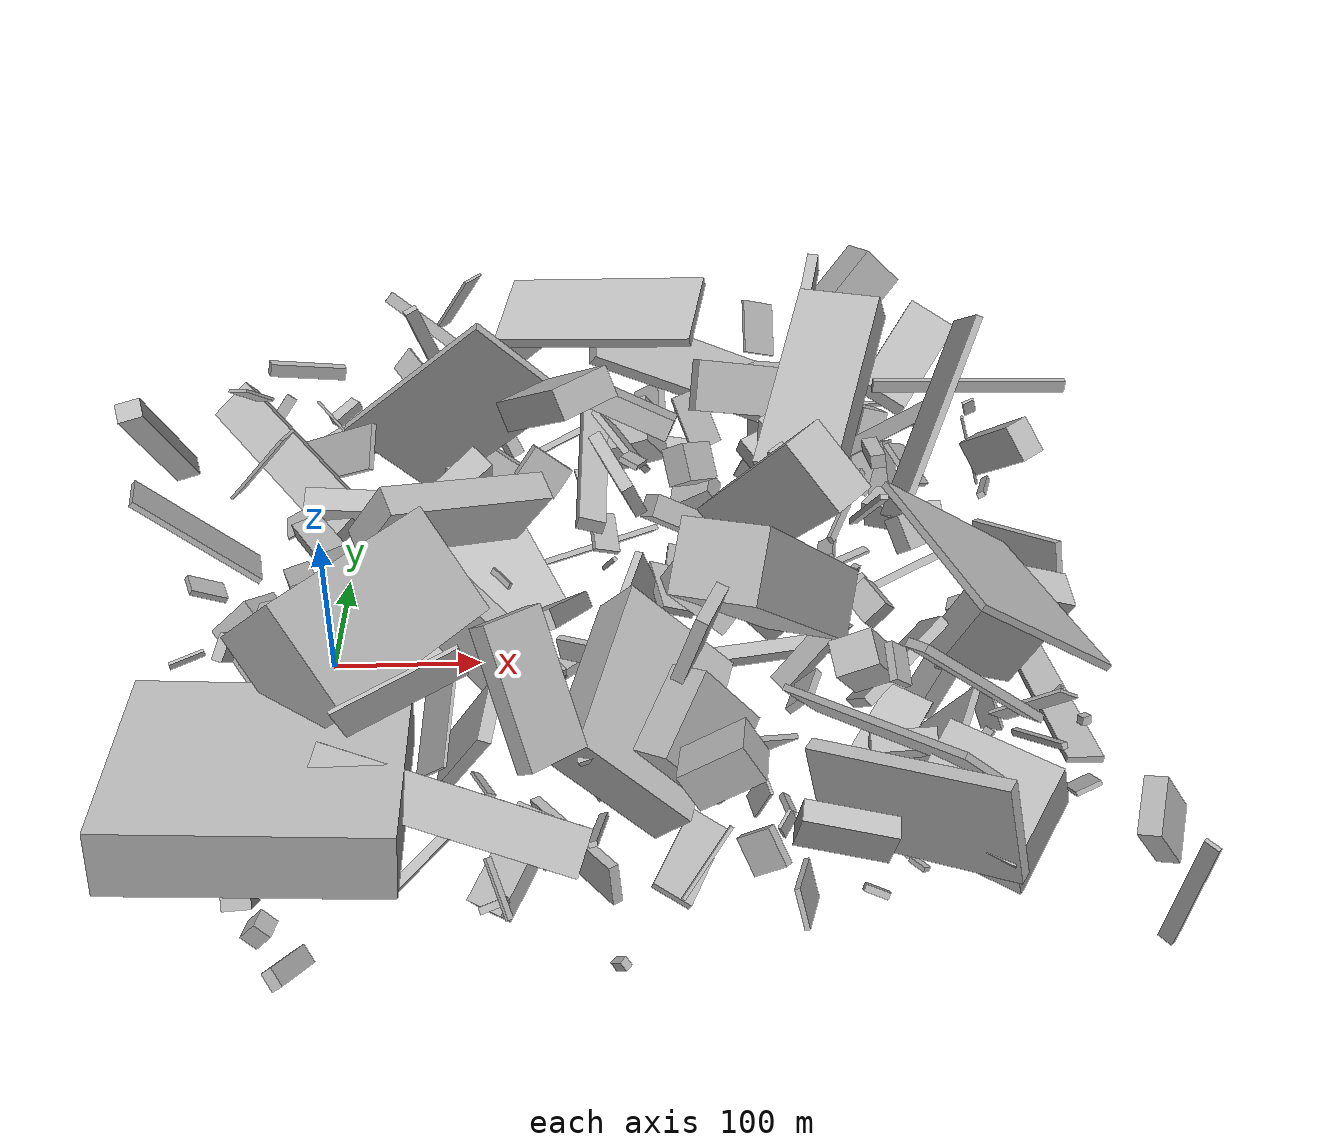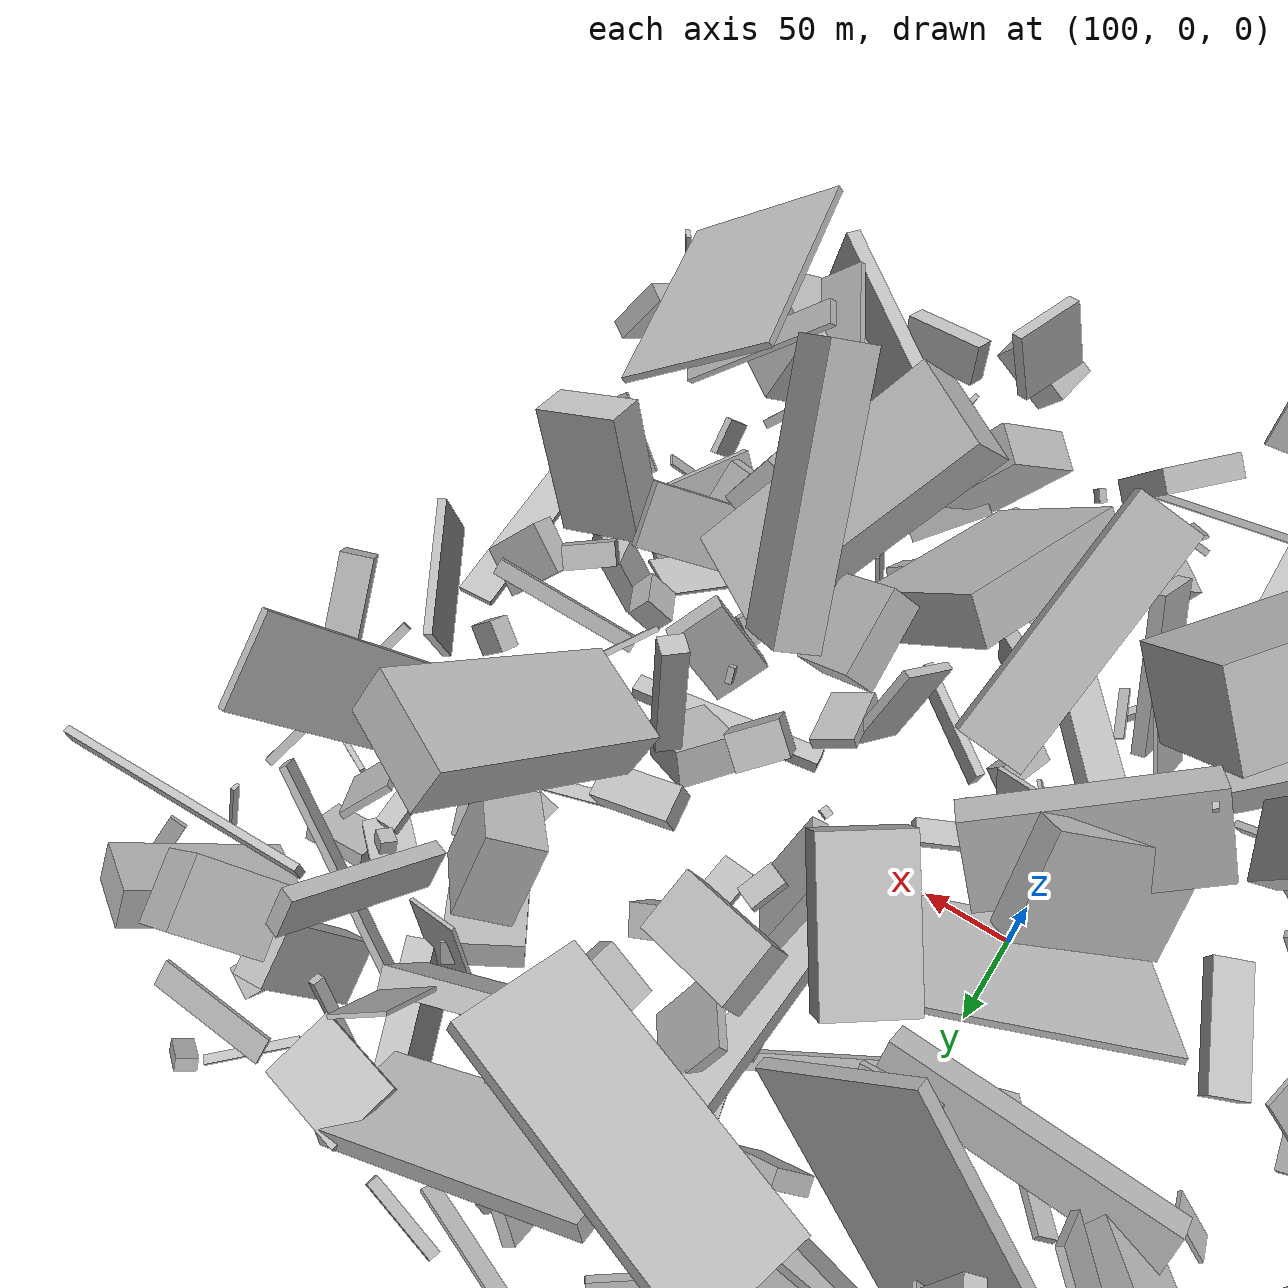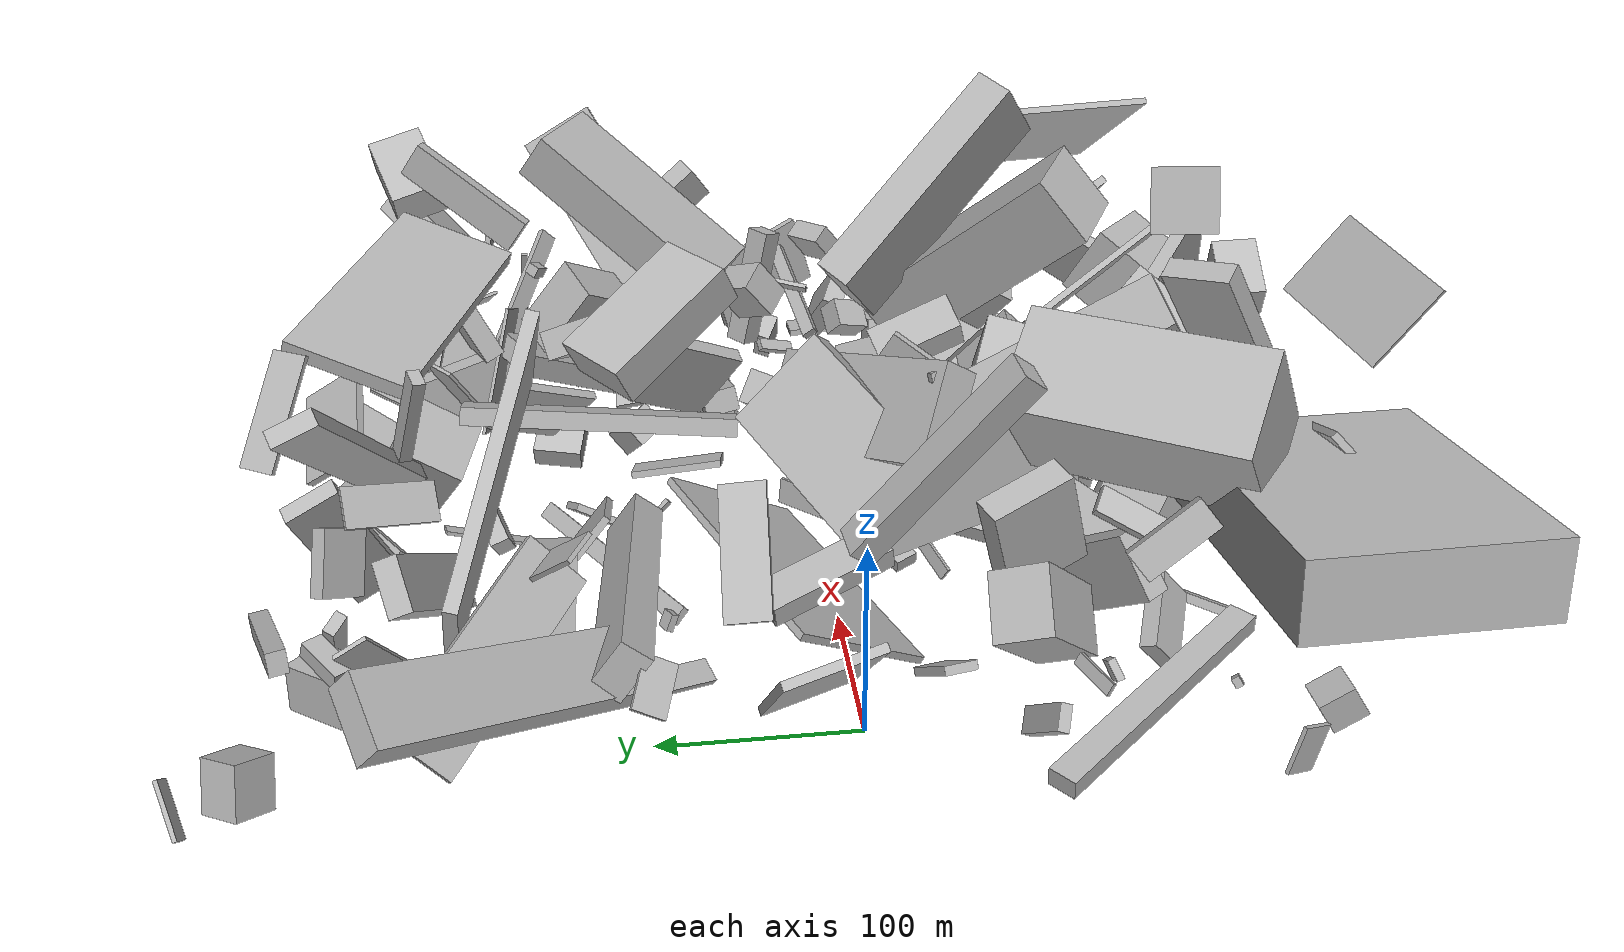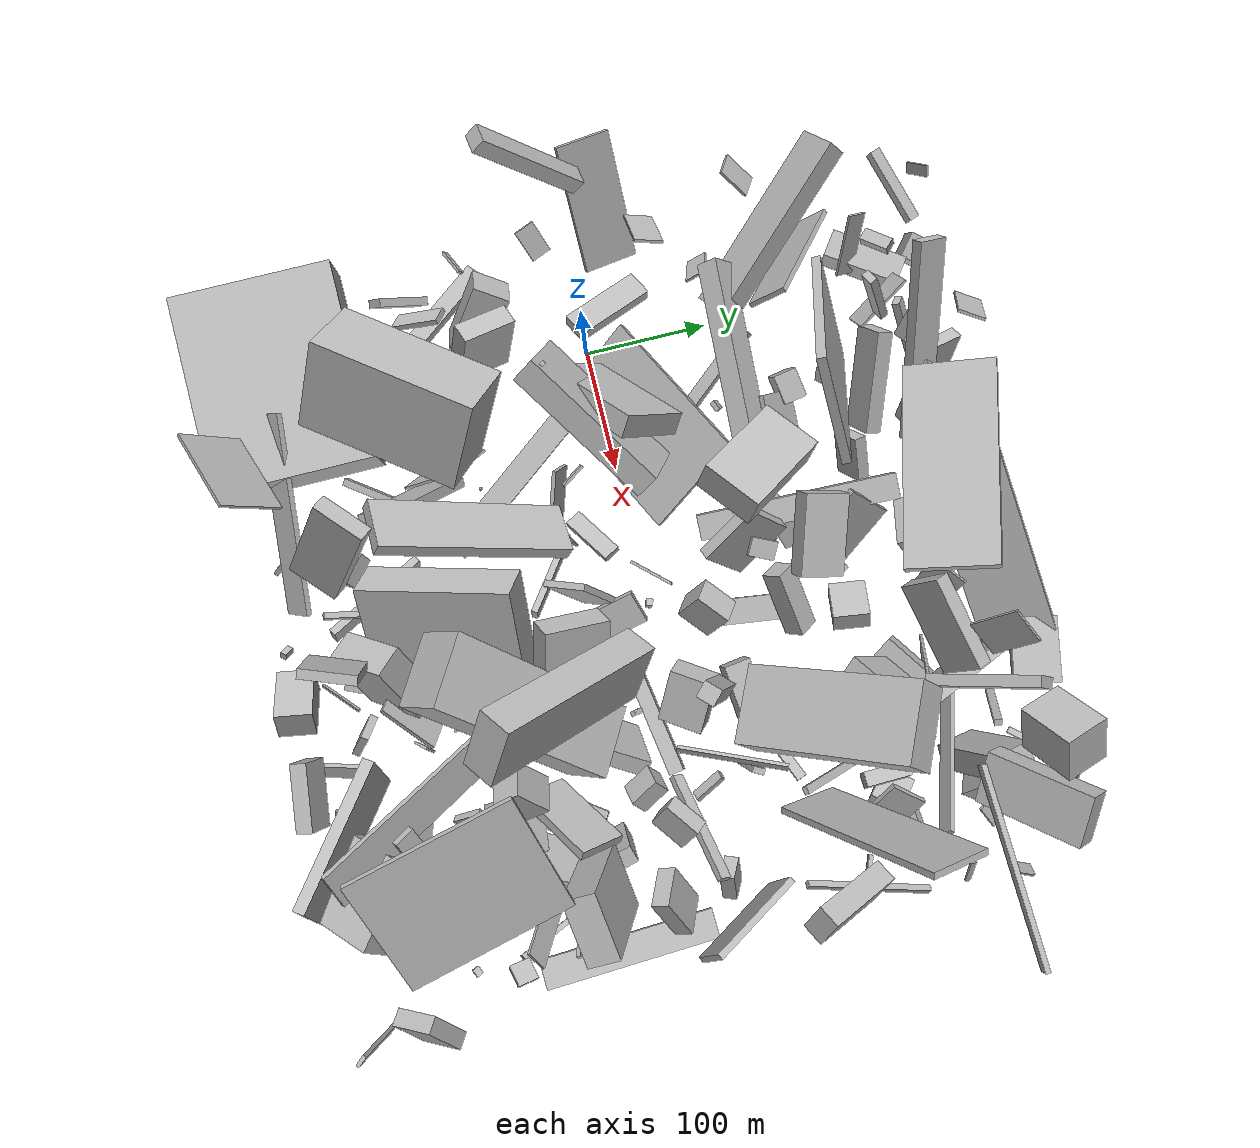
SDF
<sdf version="1.6">
 <world name="default">
  <scene>
   <sky><clouds><speed>12</speed></clouds></sky>
   <ambient>0.4 0.4 0.4 1</ambient>
   <background>0.7 0.7 0.7 1</background>
   <shadows>1</shadows>
  </scene>
  <gravity>0 0 -9.8066</gravity>
  <magnetic_field>6e-06 2.3e-05 -4.2e-05</magnetic_field>
  <physics default="0" name="default_physics" type="ode">
   <ode>
    <solver>
     <type>quick</type>
     <iters>10</iters>
     <sor>1.0</sor>
     <use_dynamic_moi_rescaling>0</use_dynamic_moi_rescaling>
    </solver>
    <constraints>
     <cfm>0</cfm>
     <erp>0.2</erp>
     <contact_max_correcting_vel>100</contact_max_correcting_vel>
     <contact_surface_layer>0.001</contact_surface_layer>
    </constraints>
   </ode>
   <max_step_size>0.004</max_step_size>
   <real_time_factor>1</real_time_factor>
   <real_time_update_rate>250</real_time_update_rate>
  </physics>
  <light name="sun" type="directional">
   <pose>0 0 10 0 0 0</pose>
   <diffuse>0.8 0.8 0.8 1</diffuse>
   <specular>0.2 0.2 0.2 1</specular>
   <attenuation>
    <range>1000</range>
    <constant>0.9</constant>
    <linear>0.01</linear>
    <quadratic>0.001</quadratic>
   </attenuation>
   <direction>-0.5 0.1 -0.9</direction>
  </light>
  <model name="building_1">
   <static>0</static>
   <pose>-15.40946905120093 48.489235072548475 83.47796572263684 0.6606610286150101 1.3319498400195333 -0.47602117565657454</pose>
   <link name="link">
    <gravity>0</gravity>
    <pose>0 0 31.5 0 0 0</pose>
    <collision name="collision"><geometry><box><size>10 20 63</size></box></geometry></collision>
    <visual name="visual">
     <cast_shadows>0</cast_shadows>
     <geometry><box><size>10 20 63</size></box></geometry>
     <material>
      <script>
       <uri>model://HANNAS_wall/materials/scripts</uri>
       <uri>model://HANNAS_wall/materials/textures</uri>
       <name>vrc/HANNAS_wall</name>
      </script>
     </material>
    </visual>
   </link>
  </model>
  <model name="building_2">
   <static>0</static>
   <pose>387.47691240882835 -232.77425235303443 61.18344624210831 0.5333309283170092 0.0370196419224653 -0.6642562123319025</pose>
   <link name="link">
    <gravity>0</gravity>
    <pose>0 0 24.0 0 0 0</pose>
    <collision name="collision"><geometry><box><size>65 58 48</size></box></geometry></collision>
    <visual name="visual">
     <cast_shadows>0</cast_shadows>
     <geometry><box><size>65 58 48</size></box></geometry>
     <material>
      <script>
       <uri>model://HANNAS_wall/materials/scripts</uri>
       <uri>model://HANNAS_wall/materials/textures</uri>
       <name>vrc/HANNAS_wall</name>
      </script>
     </material>
    </visual>
   </link>
  </model>
  <model name="building_3">
   <static>0</static>
   <pose>195.42026539088207 225.33793126762018 46.4104570934266 1.0816639850656091 -0.5606428929745272 1.5744096195411685</pose>
   <link name="link">
    <gravity>0</gravity>
    <pose>0 0 20.0 0 0 0</pose>
    <collision name="collision"><geometry><box><size>39 35 40</size></box></geometry></collision>
    <visual name="visual">
     <cast_shadows>0</cast_shadows>
     <geometry><box><size>39 35 40</size></box></geometry>
     <material>
      <script>
       <uri>model://HANNAS_wall/materials/scripts</uri>
       <uri>model://HANNAS_wall/materials/textures</uri>
       <name>vrc/HANNAS_wall</name>
      </script>
     </material>
    </visual>
   </link>
  </model>
  <model name="building_4">
   <static>0</static>
   <pose>390.6471095248768 -58.76286889954505 28.261289857396083 1.7534174453975628 -1.1772123350390233 0.0813670237640898</pose>
   <link name="link">
    <gravity>0</gravity>
    <pose>0 0 10.0 0 0 0</pose>
    <collision name="collision"><geometry><box><size>44 14 20</size></box></geometry></collision>
    <visual name="visual">
     <cast_shadows>0</cast_shadows>
     <geometry><box><size>44 14 20</size></box></geometry>
     <material>
      <script>
       <uri>model://HANNAS_wall/materials/scripts</uri>
       <uri>model://HANNAS_wall/materials/textures</uri>
       <name>vrc/HANNAS_wall</name>
      </script>
     </material>
    </visual>
   </link>
  </model>
  <model name="building_5">
   <static>0</static>
   <pose>4.289686830241401 106.98644001515282 44.70392333417334 -1.091598469408559 0.807118646782974 1.0866225300215115</pose>
   <link name="link">
    <gravity>0</gravity>
    <pose>0 0 75.0 0 0 0</pose>
    <collision name="collision"><geometry><box><size>16 34 150</size></box></geometry></collision>
    <visual name="visual">
     <cast_shadows>0</cast_shadows>
     <geometry><box><size>16 34 150</size></box></geometry>
     <material>
      <script>
       <uri>model://HANNAS_wall/materials/scripts</uri>
       <uri>model://HANNAS_wall/materials/textures</uri>
       <name>vrc/HANNAS_wall</name>
      </script>
     </material>
    </visual>
   </link>
  </model>
  <model name="building_6">
   <static>0</static>
   <pose>122.95587060061723 104.81987621062243 53.38466403227626 1.4836463431051559 -0.9303164788773728 -1.551403772637376</pose>
   <link name="link">
    <gravity>0</gravity>
    <pose>0 0 75.0 0 0 0</pose>
    <collision name="collision"><geometry><box><size>26 17 150</size></box></geometry></collision>
    <visual name="visual">
     <cast_shadows>0</cast_shadows>
     <geometry><box><size>26 17 150</size></box></geometry>
     <material>
      <script>
       <uri>model://HANNAS_wall/materials/scripts</uri>
       <uri>model://HANNAS_wall/materials/textures</uri>
       <name>vrc/HANNAS_wall</name>
      </script>
     </material>
    </visual>
   </link>
  </model>
  <model name="building_7">
   <static>0</static>
   <pose>86.05593611526285 247.12048544273426 112.0473980282739 1.0489275624526189 0.6383340337828773 -0.2031847273433447</pose>
   <link name="link">
    <gravity>0</gravity>
    <pose>0 0 11.5 0 0 0</pose>
    <collision name="collision"><geometry><box><size>150 9 23</size></box></geometry></collision>
    <visual name="visual">
     <cast_shadows>0</cast_shadows>
     <geometry><box><size>150 9 23</size></box></geometry>
     <material>
      <script>
       <uri>model://HANNAS_wall/materials/scripts</uri>
       <uri>model://HANNAS_wall/materials/textures</uri>
       <name>vrc/HANNAS_wall</name>
      </script>
     </material>
    </visual>
   </link>
  </model>
  <model name="building_8">
   <static>0</static>
   <pose>345.8888367723806 -257.60691258758914 63.351803148838925 0.0902114704054743 -0.20962358882046353 -0.6115045855052065</pose>
   <link name="link">
    <gravity>0</gravity>
    <pose>0 0 31.0 0 0 0</pose>
    <collision name="collision"><geometry><box><size>113 9 62</size></box></geometry></collision>
    <visual name="visual">
     <cast_shadows>0</cast_shadows>
     <geometry><box><size>113 9 62</size></box></geometry>
     <material>
      <script>
       <uri>model://HANNAS_wall/materials/scripts</uri>
       <uri>model://HANNAS_wall/materials/textures</uri>
       <name>vrc/HANNAS_wall</name>
      </script>
     </material>
    </visual>
   </link>
  </model>
  <model name="building_9">
   <static>0</static>
   <pose>272.92304885389206 -124.40356035833818 121.81456329137009 0.6888763508246173 0.15438052560395862 2.6262330043297193</pose>
   <link name="link">
    <gravity>0</gravity>
    <pose>0 0 22.0 0 0 0</pose>
    <collision name="collision"><geometry><box><size>53 150 44</size></box></geometry></collision>
    <visual name="visual">
     <cast_shadows>0</cast_shadows>
     <geometry><box><size>53 150 44</size></box></geometry>
     <material>
      <script>
       <uri>model://HANNAS_wall/materials/scripts</uri>
       <uri>model://HANNAS_wall/materials/textures</uri>
       <name>vrc/HANNAS_wall</name>
      </script>
     </material>
    </visual>
   </link>
  </model>
  <model name="building_10">
   <static>0</static>
   <pose>331.76769654741463 -203.73249671786567 100.63112434152454 0.4676449679763307 -0.7483035096177024 -2.924746968950336</pose>
   <link name="link">
    <gravity>0</gravity>
    <pose>0 0 2.0 0 0 0</pose>
    <collision name="collision"><geometry><box><size>31 150 4</size></box></geometry></collision>
    <visual name="visual">
     <cast_shadows>0</cast_shadows>
     <geometry><box><size>31 150 4</size></box></geometry>
     <material>
      <script>
       <uri>model://HANNAS_wall/materials/scripts</uri>
       <uri>model://HANNAS_wall/materials/textures</uri>
       <name>vrc/HANNAS_wall</name>
      </script>
     </material>
    </visual>
   </link>
  </model>
  <model name="building_11">
   <static>0</static>
   <pose>-14.267220052164674 169.54531389760345 66.5304165311198 0.9552909154097537 -0.49813086864645206 -0.6816171053956798</pose>
   <link name="link">
    <gravity>0</gravity>
    <pose>0 0 2.0 0 0 0</pose>
    <collision name="collision"><geometry><box><size>106 34 4</size></box></geometry></collision>
    <visual name="visual">
     <cast_shadows>0</cast_shadows>
     <geometry><box><size>106 34 4</size></box></geometry>
     <material>
      <script>
       <uri>model://HANNAS_wall/materials/scripts</uri>
       <uri>model://HANNAS_wall/materials/textures</uri>
       <name>vrc/HANNAS_wall</name>
      </script>
     </material>
    </visual>
   </link>
  </model>
  <model name="building_12">
   <static>0</static>
   <pose>159.26316855926473 -209.3865946689082 25.733481319758745 1.5601258000710014 -1.3874925622981942 2.1170049912540003</pose>
   <link name="link">
    <gravity>0</gravity>
    <pose>0 0 3.0 0 0 0</pose>
    <collision name="collision"><geometry><box><size>24 87 6</size></box></geometry></collision>
    <visual name="visual">
     <cast_shadows>0</cast_shadows>
     <geometry><box><size>24 87 6</size></box></geometry>
     <material>
      <script>
       <uri>model://HANNAS_wall/materials/scripts</uri>
       <uri>model://HANNAS_wall/materials/textures</uri>
       <name>vrc/HANNAS_wall</name>
      </script>
     </material>
    </visual>
   </link>
  </model>
  <model name="building_13">
   <static>0</static>
   <pose>98.34963933505558 -73.62403496290293 56.5721595581413 -0.11014615248948859 -0.19115786663829787 -2.481758304729141</pose>
   <link name="link">
    <gravity>0</gravity>
    <pose>0 0 22.5 0 0 0</pose>
    <collision name="collision"><geometry><box><size>18 150 45</size></box></geometry></collision>
    <visual name="visual">
     <cast_shadows>0</cast_shadows>
     <geometry><box><size>18 150 45</size></box></geometry>
     <material>
      <script>
       <uri>model://HANNAS_wall/materials/scripts</uri>
       <uri>model://HANNAS_wall/materials/textures</uri>
       <name>vrc/HANNAS_wall</name>
      </script>
     </material>
    </visual>
   </link>
  </model>
  <model name="building_14">
   <static>0</static>
   <pose>361.18956088800326 7.607705224751195 44.17378770220947 0.46122984612862505 0.7898631440260956 0.827923298537248</pose>
   <link name="link">
    <gravity>0</gravity>
    <pose>0 0 4.0 0 0 0</pose>
    <collision name="collision"><geometry><box><size>4 26 8</size></box></geometry></collision>
    <visual name="visual">
     <cast_shadows>0</cast_shadows>
     <geometry><box><size>4 26 8</size></box></geometry>
     <material>
      <script>
       <uri>model://HANNAS_wall/materials/scripts</uri>
       <uri>model://HANNAS_wall/materials/textures</uri>
       <name>vrc/HANNAS_wall</name>
      </script>
     </material>
    </visual>
   </link>
  </model>
  <model name="building_15">
   <static>0</static>
   <pose>394.6074532804525 197.6504539244415 103.86973596358992 -2.7165729200526 1.5254399712984126 -2.6794360454240707</pose>
   <link name="link">
    <gravity>0</gravity>
    <pose>0 0 75.0 0 0 0</pose>
    <collision name="collision"><geometry><box><size>10 4 150</size></box></geometry></collision>
    <visual name="visual">
     <cast_shadows>0</cast_shadows>
     <geometry><box><size>10 4 150</size></box></geometry>
     <material>
      <script>
       <uri>model://HANNAS_wall/materials/scripts</uri>
       <uri>model://HANNAS_wall/materials/textures</uri>
       <name>vrc/HANNAS_wall</name>
      </script>
     </material>
    </visual>
   </link>
  </model>
  <model name="building_16">
   <static>0</static>
   <pose>155.37633494674714 -52.24556168026713 80.04553700217986 0.9869160135221994 -0.36446205391433656 0.06837988870615896</pose>
   <link name="link">
    <gravity>0</gravity>
    <pose>0 0 75.0 0 0 0</pose>
    <collision name="collision"><geometry><box><size>40 11 150</size></box></geometry></collision>
    <visual name="visual">
     <cast_shadows>0</cast_shadows>
     <geometry><box><size>40 11 150</size></box></geometry>
     <material>
      <script>
       <uri>model://HANNAS_wall/materials/scripts</uri>
       <uri>model://HANNAS_wall/materials/textures</uri>
       <name>vrc/HANNAS_wall</name>
      </script>
     </material>
    </visual>
   </link>
  </model>
  <model name="building_17">
   <static>0</static>
   <pose>193.70871926552255 -146.8150998121074 68.54899901740694 0.7487934997552398 -0.20692695145643705 1.2775613620409565</pose>
   <link name="link">
    <gravity>0</gravity>
    <pose>0 0 15.5 0 0 0</pose>
    <collision name="collision"><geometry><box><size>118 82 31</size></box></geometry></collision>
    <visual name="visual">
     <cast_shadows>0</cast_shadows>
     <geometry><box><size>118 82 31</size></box></geometry>
     <material>
      <script>
       <uri>model://HANNAS_wall/materials/scripts</uri>
       <uri>model://HANNAS_wall/materials/textures</uri>
       <name>vrc/HANNAS_wall</name>
      </script>
     </material>
    </visual>
   </link>
  </model>
  <model name="building_18">
   <static>0</static>
   <pose>104.79416934999136 -142.50146671710775 73.63118417303832 -2.4351214966518304 0.9421025663159311 2.1706856656243505</pose>
   <link name="link">
    <gravity>0</gravity>
    <pose>0 0 17.5 0 0 0</pose>
    <collision name="collision"><geometry><box><size>94 8 35</size></box></geometry></collision>
    <visual name="visual">
     <cast_shadows>0</cast_shadows>
     <geometry><box><size>94 8 35</size></box></geometry>
     <material>
      <script>
       <uri>model://HANNAS_wall/materials/scripts</uri>
       <uri>model://HANNAS_wall/materials/textures</uri>
       <name>vrc/HANNAS_wall</name>
      </script>
     </material>
    </visual>
   </link>
  </model>
  <model name="building_19">
   <static>0</static>
   <pose>341.5602806695067 120.80445464012655 82.78740405948585 0.8009391516269025 -0.9096102685809624 -1.7142213834626716</pose>
   <link name="link">
    <gravity>0</gravity>
    <pose>0 0 22.5 0 0 0</pose>
    <collision name="collision"><geometry><box><size>49 31 45</size></box></geometry></collision>
    <visual name="visual">
     <cast_shadows>0</cast_shadows>
     <geometry><box><size>49 31 45</size></box></geometry>
     <material>
      <script>
       <uri>model://HANNAS_wall/materials/scripts</uri>
       <uri>model://HANNAS_wall/materials/textures</uri>
       <name>vrc/HANNAS_wall</name>
      </script>
     </material>
    </visual>
   </link>
  </model>
  <model name="building_20">
   <static>0</static>
   <pose>417.2304267297484 112.18557234560535 122.82527183178273 2.19859053724062 -0.913077147811763 0.9089554446490067</pose>
   <link name="link">
    <gravity>0</gravity>
    <pose>0 0 2.5 0 0 0</pose>
    <collision name="collision"><geometry><box><size>150 50 5</size></box></geometry></collision>
    <visual name="visual">
     <cast_shadows>0</cast_shadows>
     <geometry><box><size>150 50 5</size></box></geometry>
     <material>
      <script>
       <uri>model://HANNAS_wall/materials/scripts</uri>
       <uri>model://HANNAS_wall/materials/textures</uri>
       <name>vrc/HANNAS_wall</name>
      </script>
     </material>
    </visual>
   </link>
  </model>
  <model name="building_21">
   <static>0</static>
   <pose>70.37461976060183 237.06652039944748 69.15286060212185 -0.5755333490579132 -1.090583508413947 -0.1477828022766647</pose>
   <link name="link">
    <gravity>0</gravity>
    <pose>0 0 12.0 0 0 0</pose>
    <collision name="collision"><geometry><box><size>33 9 24</size></box></geometry></collision>
    <visual name="visual">
     <cast_shadows>0</cast_shadows>
     <geometry><box><size>33 9 24</size></box></geometry>
     <material>
      <script>
       <uri>model://HANNAS_wall/materials/scripts</uri>
       <uri>model://HANNAS_wall/materials/textures</uri>
       <name>vrc/HANNAS_wall</name>
      </script>
     </material>
    </visual>
   </link>
  </model>
  <model name="building_22">
   <static>0</static>
   <pose>251.34620506691274 245.95248171115813 105.09104993950115 2.676579680342008 -0.45922151447739257 -2.953209946280549</pose>
   <link name="link">
    <gravity>0</gravity>
    <pose>0 0 5.0 0 0 0</pose>
    <collision name="collision"><geometry><box><size>150 54 10</size></box></geometry></collision>
    <visual name="visual">
     <cast_shadows>0</cast_shadows>
     <geometry><box><size>150 54 10</size></box></geometry>
     <material>
      <script>
       <uri>model://HANNAS_wall/materials/scripts</uri>
       <uri>model://HANNAS_wall/materials/textures</uri>
       <name>vrc/HANNAS_wall</name>
      </script>
     </material>
    </visual>
   </link>
  </model>
  <model name="building_23">
   <static>0</static>
   <pose>80.61699406453974 -93.43775193594135 138.2223505600222 -1.549271311401299 0.7446437284315558 2.5178109987744084</pose>
   <link name="link">
    <gravity>0</gravity>
    <pose>0 0 60.5 0 0 0</pose>
    <collision name="collision"><geometry><box><size>55 71 121</size></box></geometry></collision>
    <visual name="visual">
     <cast_shadows>0</cast_shadows>
     <geometry><box><size>55 71 121</size></box></geometry>
     <material>
      <script>
       <uri>model://HANNAS_wall/materials/scripts</uri>
       <uri>model://HANNAS_wall/materials/textures</uri>
       <name>vrc/HANNAS_wall</name>
      </script>
     </material>
    </visual>
   </link>
  </model>
  <model name="building_24">
   <static>0</static>
   <pose>-37.57711728249996 -135.03972867335196 31.527295860020246 1.0150946047471558 -1.465987361438521 2.8180148281602126</pose>
   <link name="link">
    <gravity>0</gravity>
    <pose>0 0 7.0 0 0 0</pose>
    <collision name="collision"><geometry><box><size>9 150 14</size></box></geometry></collision>
    <visual name="visual">
     <cast_shadows>0</cast_shadows>
     <geometry><box><size>9 150 14</size></box></geometry>
     <material>
      <script>
       <uri>model://HANNAS_wall/materials/scripts</uri>
       <uri>model://HANNAS_wall/materials/textures</uri>
       <name>vrc/HANNAS_wall</name>
      </script>
     </material>
    </visual>
   </link>
  </model>
  <model name="building_25">
   <static>0</static>
   <pose>22.72459754273749 -157.43585097709703 28.922503526487564 0.5013023883560919 0.5685327370787435 2.7574304789780997</pose>
   <link name="link">
    <gravity>0</gravity>
    <pose>0 0 12.0 0 0 0</pose>
    <collision name="collision"><geometry><box><size>40 9 24</size></box></geometry></collision>
    <visual name="visual">
     <cast_shadows>0</cast_shadows>
     <geometry><box><size>40 9 24</size></box></geometry>
     <material>
      <script>
       <uri>model://HANNAS_wall/materials/scripts</uri>
       <uri>model://HANNAS_wall/materials/textures</uri>
       <name>vrc/HANNAS_wall</name>
      </script>
     </material>
    </visual>
   </link>
  </model>
  <model name="building_26">
   <static>0</static>
   <pose>264.3776197506206 107.7759199272938 34.483710147613294 0.9307663108238379 -0.488208672427251 -1.0236264390822123</pose>
   <link name="link">
    <gravity>0</gravity>
    <pose>0 0 27.0 0 0 0</pose>
    <collision name="collision"><geometry><box><size>18 17 54</size></box></geometry></collision>
    <visual name="visual">
     <cast_shadows>0</cast_shadows>
     <geometry><box><size>18 17 54</size></box></geometry>
     <material>
      <script>
       <uri>model://HANNAS_wall/materials/scripts</uri>
       <uri>model://HANNAS_wall/materials/textures</uri>
       <name>vrc/HANNAS_wall</name>
      </script>
     </material>
    </visual>
   </link>
  </model>
  <model name="building_27">
   <static>0</static>
   <pose>-22.34228868039463 -135.55675207586208 107.04717480337376 0.810987057291575 -0.8418935043621446 -2.793033945021948</pose>
   <link name="link">
    <gravity>0</gravity>
    <pose>0 0 20.0 0 0 0</pose>
    <collision name="collision"><geometry><box><size>4 14 40</size></box></geometry></collision>
    <visual name="visual">
     <cast_shadows>0</cast_shadows>
     <geometry><box><size>4 14 40</size></box></geometry>
     <material>
      <script>
       <uri>model://HANNAS_wall/materials/scripts</uri>
       <uri>model://HANNAS_wall/materials/textures</uri>
       <name>vrc/HANNAS_wall</name>
      </script>
     </material>
    </visual>
   </link>
  </model>
  <model name="building_28">
   <static>0</static>
   <pose>341.15803810802186 105.51661331929368 143.50354329104098 -0.07487670340606903 -0.6531098428401786 1.1795823281506679</pose>
   <link name="link">
    <gravity>0</gravity>
    <pose>0 0 14.5 0 0 0</pose>
    <collision name="collision"><geometry><box><size>134 57 29</size></box></geometry></collision>
    <visual name="visual">
     <cast_shadows>0</cast_shadows>
     <geometry><box><size>134 57 29</size></box></geometry>
     <material>
      <script>
       <uri>model://HANNAS_wall/materials/scripts</uri>
       <uri>model://HANNAS_wall/materials/textures</uri>
       <name>vrc/HANNAS_wall</name>
      </script>
     </material>
    </visual>
   </link>
  </model>
  <model name="building_29">
   <static>0</static>
   <pose>411.2942130548839 239.27422375140117 30.969162911148302 -2.7449404133757573 -0.3654711604372377 -2.1668315379713925</pose>
   <link name="link">
    <gravity>0</gravity>
    <pose>0 0 25.0 0 0 0</pose>
    <collision name="collision"><geometry><box><size>21 18 50</size></box></geometry></collision>
    <visual name="visual">
     <cast_shadows>0</cast_shadows>
     <geometry><box><size>21 18 50</size></box></geometry>
     <material>
      <script>
       <uri>model://HANNAS_wall/materials/scripts</uri>
       <uri>model://HANNAS_wall/materials/textures</uri>
       <name>vrc/HANNAS_wall</name>
      </script>
     </material>
    </visual>
   </link>
  </model>
  <model name="building_30">
   <static>0</static>
   <pose>359.87840974603824 -81.67283586071687 53.30240212858959 0.7502803925968211 -0.49605957477824936 0.6113311302998181</pose>
   <link name="link">
    <gravity>0</gravity>
    <pose>0 0 19.5 0 0 0</pose>
    <collision name="collision"><geometry><box><size>70 7 39</size></box></geometry></collision>
    <visual name="visual">
     <cast_shadows>0</cast_shadows>
     <geometry><box><size>70 7 39</size></box></geometry>
     <material>
      <script>
       <uri>model://HANNAS_wall/materials/scripts</uri>
       <uri>model://HANNAS_wall/materials/textures</uri>
       <name>vrc/HANNAS_wall</name>
      </script>
     </material>
    </visual>
   </link>
  </model>
  <model name="building_31">
   <static>0</static>
   <pose>309.3869612737192 139.2884420406525 56.555057493158785 1.4427853762859233 -0.4544701253354884 2.2023761404183633</pose>
   <link name="link">
    <gravity>0</gravity>
    <pose>0 0 20.0 0 0 0</pose>
    <collision name="collision"><geometry><box><size>73 14 40</size></box></geometry></collision>
    <visual name="visual">
     <cast_shadows>0</cast_shadows>
     <geometry><box><size>73 14 40</size></box></geometry>
     <material>
      <script>
       <uri>model://HANNAS_wall/materials/scripts</uri>
       <uri>model://HANNAS_wall/materials/textures</uri>
       <name>vrc/HANNAS_wall</name>
      </script>
     </material>
    </visual>
   </link>
  </model>
  <model name="building_32">
   <static>0</static>
   <pose>320.216310687661 209.56693527866082 38.49452775688098 1.8797287416360433 -1.3839018905859348 1.6574840775523225</pose>
   <link name="link">
    <gravity>0</gravity>
    <pose>0 0 7.5 0 0 0</pose>
    <collision name="collision"><geometry><box><size>42 71 15</size></box></geometry></collision>
    <visual name="visual">
     <cast_shadows>0</cast_shadows>
     <geometry><box><size>42 71 15</size></box></geometry>
     <material>
      <script>
       <uri>model://HANNAS_wall/materials/scripts</uri>
       <uri>model://HANNAS_wall/materials/textures</uri>
       <name>vrc/HANNAS_wall</name>
      </script>
     </material>
    </visual>
   </link>
  </model>
  <model name="building_33">
   <static>0</static>
   <pose>78.67021711334705 168.64807966165193 101.07768995363624 1.1875644406153136 -0.7772437303030574 -2.9666430102252206</pose>
   <link name="link">
    <gravity>0</gravity>
    <pose>0 0 3.5 0 0 0</pose>
    <collision name="collision"><geometry><box><size>90 150 7</size></box></geometry></collision>
    <visual name="visual">
     <cast_shadows>0</cast_shadows>
     <geometry><box><size>90 150 7</size></box></geometry>
     <material>
      <script>
       <uri>model://HANNAS_wall/materials/scripts</uri>
       <uri>model://HANNAS_wall/materials/textures</uri>
       <name>vrc/HANNAS_wall</name>
      </script>
     </material>
    </visual>
   </link>
  </model>
  <model name="building_34">
   <static>0</static>
   <pose>131.39393463632834 -229.6424532507173 36.64812475317592 -0.15618986755803943 -0.5925463786972044 0.9579126829627951</pose>
   <link name="link">
    <gravity>0</gravity>
    <pose>0 0 5.5 0 0 0</pose>
    <collision name="collision"><geometry><box><size>60 25 11</size></box></geometry></collision>
    <visual name="visual">
     <cast_shadows>0</cast_shadows>
     <geometry><box><size>60 25 11</size></box></geometry>
     <material>
      <script>
       <uri>model://HANNAS_wall/materials/scripts</uri>
       <uri>model://HANNAS_wall/materials/textures</uri>
       <name>vrc/HANNAS_wall</name>
      </script>
     </material>
    </visual>
   </link>
  </model>
  <model name="building_35">
   <static>0</static>
   <pose>185.36432006196569 265.8515931960543 39.59105831705866 1.7106849768150694 0.7193593713389123 -0.8302468885812637</pose>
   <link name="link">
    <gravity>0</gravity>
    <pose>0 0 31.0 0 0 0</pose>
    <collision name="collision"><geometry><box><size>5 4 62</size></box></geometry></collision>
    <visual name="visual">
     <cast_shadows>0</cast_shadows>
     <geometry><box><size>5 4 62</size></box></geometry>
     <material>
      <script>
       <uri>model://HANNAS_wall/materials/scripts</uri>
       <uri>model://HANNAS_wall/materials/textures</uri>
       <name>vrc/HANNAS_wall</name>
      </script>
     </material>
    </visual>
   </link>
  </model>
  <model name="building_36">
   <static>0</static>
   <pose>342.2849401513516 -116.84686768812888 77.79540004967745 0.6037028357375143 -0.47658948393516054 -0.1619288230809903</pose>
   <link name="link">
    <gravity>0</gravity>
    <pose>0 0 17.5 0 0 0</pose>
    <collision name="collision"><geometry><box><size>27 23 35</size></box></geometry></collision>
    <visual name="visual">
     <cast_shadows>0</cast_shadows>
     <geometry><box><size>27 23 35</size></box></geometry>
     <material>
      <script>
       <uri>model://HANNAS_wall/materials/scripts</uri>
       <uri>model://HANNAS_wall/materials/textures</uri>
       <name>vrc/HANNAS_wall</name>
      </script>
     </material>
    </visual>
   </link>
  </model>
  <model name="building_37">
   <static>0</static>
   <pose>125.9512153068377 131.14434400146897 47.897196419081325 1.2257859646127207 0.6727540239209071 -1.805277169994967</pose>
   <link name="link">
    <gravity>0</gravity>
    <pose>0 0 21.5 0 0 0</pose>
    <collision name="collision"><geometry><box><size>4 42 43</size></box></geometry></collision>
    <visual name="visual">
     <cast_shadows>0</cast_shadows>
     <geometry><box><size>4 42 43</size></box></geometry>
     <material>
      <script>
       <uri>model://HANNAS_wall/materials/scripts</uri>
       <uri>model://HANNAS_wall/materials/textures</uri>
       <name>vrc/HANNAS_wall</name>
      </script>
     </material>
    </visual>
   </link>
  </model>
  <model name="building_38">
   <static>0</static>
   <pose>-1.960090226616316 -231.7199812472217 80.37061075252245 0.015684191024329906 -0.0663345719770131 -3.134092219686488</pose>
   <link name="link">
    <gravity>0</gravity>
    <pose>0 0 20.5 0 0 0</pose>
    <collision name="collision"><geometry><box><size>150 121 41</size></box></geometry></collision>
    <visual name="visual">
     <cast_shadows>0</cast_shadows>
     <geometry><box><size>150 121 41</size></box></geometry>
     <material>
      <script>
       <uri>model://HANNAS_wall/materials/scripts</uri>
       <uri>model://HANNAS_wall/materials/textures</uri>
       <name>vrc/HANNAS_wall</name>
      </script>
     </material>
    </visual>
   </link>
  </model>
  <model name="building_39">
   <static>0</static>
   <pose>299.83355371926655 -30.885032758143225 53.788522552541146 1.5019455801414585 0.6672985578282256 -1.4701699718534331</pose>
   <link name="link">
    <gravity>0</gravity>
    <pose>0 0 2.0 0 0 0</pose>
    <collision name="collision"><geometry><box><size>4 10 4</size></box></geometry></collision>
    <visual name="visual">
     <cast_shadows>0</cast_shadows>
     <geometry><box><size>4 10 4</size></box></geometry>
     <material>
      <script>
       <uri>model://HANNAS_wall/materials/scripts</uri>
       <uri>model://HANNAS_wall/materials/textures</uri>
       <name>vrc/HANNAS_wall</name>
      </script>
     </material>
    </visual>
   </link>
  </model>
  <model name="building_40">
   <static>0</static>
   <pose>266.2120642946768 -26.620576289741024 122.58345999955213 -0.40352274067392807 -0.7231917506955453 2.4971370081185684</pose>
   <link name="link">
    <gravity>0</gravity>
    <pose>0 0 75.0 0 0 0</pose>
    <collision name="collision"><geometry><box><size>47 25 150</size></box></geometry></collision>
    <visual name="visual">
     <cast_shadows>0</cast_shadows>
     <geometry><box><size>47 25 150</size></box></geometry>
     <material>
      <script>
       <uri>model://HANNAS_wall/materials/scripts</uri>
       <uri>model://HANNAS_wall/materials/textures</uri>
       <name>vrc/HANNAS_wall</name>
      </script>
     </material>
    </visual>
   </link>
  </model>
  <model name="building_41">
   <static>0</static>
   <pose>168.27194507166797 -205.04260983572613 93.51818992525773 -2.7493861265278596 0.4067937762518701 -1.4010920545391723</pose>
   <link name="link">
    <gravity>0</gravity>
    <pose>0 0 2.5 0 0 0</pose>
    <collision name="collision"><geometry><box><size>9 9 5</size></box></geometry></collision>
    <visual name="visual">
     <cast_shadows>0</cast_shadows>
     <geometry><box><size>9 9 5</size></box></geometry>
     <material>
      <script>
       <uri>model://HANNAS_wall/materials/scripts</uri>
       <uri>model://HANNAS_wall/materials/textures</uri>
       <name>vrc/HANNAS_wall</name>
      </script>
     </material>
    </visual>
   </link>
  </model>
  <model name="building_42">
   <static>0</static>
   <pose>-31.48828384841086 -125.0776617594713 121.1426538898069 2.4626262361596534 0.3046084957295496 -0.15568096365559522</pose>
   <link name="link">
    <gravity>0</gravity>
    <pose>0 0 8.0 0 0 0</pose>
    <collision name="collision"><geometry><box><size>6 40 16</size></box></geometry></collision>
    <visual name="visual">
     <cast_shadows>0</cast_shadows>
     <geometry><box><size>6 40 16</size></box></geometry>
     <material>
      <script>
       <uri>model://HANNAS_wall/materials/scripts</uri>
       <uri>model://HANNAS_wall/materials/textures</uri>
       <name>vrc/HANNAS_wall</name>
      </script>
     </material>
    </visual>
   </link>
  </model>
  <model name="building_43">
   <static>0</static>
   <pose>243.7837416370377 105.67003840488064 20.089445007969687 -1.422617059557073 -0.214365604456762 2.9938636087067976</pose>
   <link name="link">
    <gravity>0</gravity>
    <pose>0 0 27.0 0 0 0</pose>
    <collision name="collision"><geometry><box><size>20 4 54</size></box></geometry></collision>
    <visual name="visual">
     <cast_shadows>0</cast_shadows>
     <geometry><box><size>20 4 54</size></box></geometry>
     <material>
      <script>
       <uri>model://HANNAS_wall/materials/scripts</uri>
       <uri>model://HANNAS_wall/materials/textures</uri>
       <name>vrc/HANNAS_wall</name>
      </script>
     </material>
    </visual>
   </link>
  </model>
  <model name="building_44">
   <static>0</static>
   <pose>205.85368709940622 123.36305713672164 118.00246873415858 -0.36132992266183683 -0.3562273729038361 -1.7276084758862755</pose>
   <link name="link">
    <gravity>0</gravity>
    <pose>0 0 8.0 0 0 0</pose>
    <collision name="collision"><geometry><box><size>34 60 16</size></box></geometry></collision>
    <visual name="visual">
     <cast_shadows>0</cast_shadows>
     <geometry><box><size>34 60 16</size></box></geometry>
     <material>
      <script>
       <uri>model://HANNAS_wall/materials/scripts</uri>
       <uri>model://HANNAS_wall/materials/textures</uri>
       <name>vrc/HANNAS_wall</name>
      </script>
     </material>
    </visual>
   </link>
  </model>
  <model name="building_45">
   <static>0</static>
   <pose>135.25890932713727 266.9059065566778 103.3827053272004 -0.8282006260108365 -0.5972555595209849 2.2024481975542107</pose>
   <link name="link">
    <gravity>0</gravity>
    <pose>0 0 20.0 0 0 0</pose>
    <collision name="collision"><geometry><box><size>4 49 40</size></box></geometry></collision>
    <visual name="visual">
     <cast_shadows>0</cast_shadows>
     <geometry><box><size>4 49 40</size></box></geometry>
     <material>
      <script>
       <uri>model://HANNAS_wall/materials/scripts</uri>
       <uri>model://HANNAS_wall/materials/textures</uri>
       <name>vrc/HANNAS_wall</name>
      </script>
     </material>
    </visual>
   </link>
  </model>
  <model name="building_46">
   <static>0</static>
   <pose>252.51493734272725 147.72913208864983 46.98714959127847 3.026870483716338 0.548085571897788 2.9336742100093134</pose>
   <link name="link">
    <gravity>0</gravity>
    <pose>0 0 8.0 0 0 0</pose>
    <collision name="collision"><geometry><box><size>33 28 16</size></box></geometry></collision>
    <visual name="visual">
     <cast_shadows>0</cast_shadows>
     <geometry><box><size>33 28 16</size></box></geometry>
     <material>
      <script>
       <uri>model://HANNAS_wall/materials/scripts</uri>
       <uri>model://HANNAS_wall/materials/textures</uri>
       <name>vrc/HANNAS_wall</name>
      </script>
     </material>
    </visual>
   </link>
  </model>
  <model name="building_47">
   <static>0</static>
   <pose>449.4952539522483 -85.35931132954619 80.66650673376047 1.2352251398997536 0.26587010401900946 -1.5429356963920489</pose>
   <link name="link">
    <gravity>0</gravity>
    <pose>0 0 26.5 0 0 0</pose>
    <collision name="collision"><geometry><box><size>25 78 53</size></box></geometry></collision>
    <visual name="visual">
     <cast_shadows>0</cast_shadows>
     <geometry><box><size>25 78 53</size></box></geometry>
     <material>
      <script>
       <uri>model://HANNAS_wall/materials/scripts</uri>
       <uri>model://HANNAS_wall/materials/textures</uri>
       <name>vrc/HANNAS_wall</name>
      </script>
     </material>
    </visual>
   </link>
  </model>
  <model name="building_48">
   <static>0</static>
   <pose>80.46253854953413 26.82059748431923 41.625632989670194 0.19988512551552537 0.5365792366010784 -1.025870557734511</pose>
   <link name="link">
    <gravity>0</gravity>
    <pose>0 0 2.0 0 0 0</pose>
    <collision name="collision"><geometry><box><size>88 134 4</size></box></geometry></collision>
    <visual name="visual">
     <cast_shadows>0</cast_shadows>
     <geometry><box><size>88 134 4</size></box></geometry>
     <material>
      <script>
       <uri>model://HANNAS_wall/materials/scripts</uri>
       <uri>model://HANNAS_wall/materials/textures</uri>
       <name>vrc/HANNAS_wall</name>
      </script>
     </material>
    </visual>
   </link>
  </model>
  <model name="building_49">
   <static>0</static>
   <pose>397.4522518077086 -195.28624777534426 22.009670517232298 0.05215317821713353 0.6637624886092071 1.5866088578147248</pose>
   <link name="link">
    <gravity>0</gravity>
    <pose>0 0 14.0 0 0 0</pose>
    <collision name="collision"><geometry><box><size>23 4 28</size></box></geometry></collision>
    <visual name="visual">
     <cast_shadows>0</cast_shadows>
     <geometry><box><size>23 4 28</size></box></geometry>
     <material>
      <script>
       <uri>model://HANNAS_wall/materials/scripts</uri>
       <uri>model://HANNAS_wall/materials/textures</uri>
       <name>vrc/HANNAS_wall</name>
      </script>
     </material>
    </visual>
   </link>
  </model>
  <model name="building_50">
   <static>0</static>
   <pose>327.47390210426 -204.1207653415575 46.906829468472424 -2.1742264689622846 -0.3657768669206217 -1.7397316014653443</pose>
   <link name="link">
    <gravity>0</gravity>
    <pose>0 0 17.0 0 0 0</pose>
    <collision name="collision"><geometry><box><size>15 15 34</size></box></geometry></collision>
    <visual name="visual">
     <cast_shadows>0</cast_shadows>
     <geometry><box><size>15 15 34</size></box></geometry>
     <material>
      <script>
       <uri>model://HANNAS_wall/materials/scripts</uri>
       <uri>model://HANNAS_wall/materials/textures</uri>
       <name>vrc/HANNAS_wall</name>
      </script>
     </material>
    </visual>
   </link>
  </model>
  <model name="building_51">
   <static>0</static>
   <pose>63.14234940966295 209.33302091371922 128.9760427014881 -0.1303777406892646 0.3729036915264912 -2.7498113966429734</pose>
   <link name="link">
    <gravity>0</gravity>
    <pose>0 0 24.0 0 0 0</pose>
    <collision name="collision"><geometry><box><size>10 6 48</size></box></geometry></collision>
    <visual name="visual">
     <cast_shadows>0</cast_shadows>
     <geometry><box><size>10 6 48</size></box></geometry>
     <material>
      <script>
       <uri>model://HANNAS_wall/materials/scripts</uri>
       <uri>model://HANNAS_wall/materials/textures</uri>
       <name>vrc/HANNAS_wall</name>
      </script>
     </material>
    </visual>
   </link>
  </model>
  <model name="building_52">
   <static>0</static>
   <pose>163.72500202545913 117.32594469219725 10.573570925350534 -3.109861516344146 -0.84118649028014 2.0622811324620764</pose>
   <link name="link">
    <gravity>0</gravity>
    <pose>0 0 5.0 0 0 0</pose>
    <collision name="collision"><geometry><box><size>4 150 10</size></box></geometry></collision>
    <visual name="visual">
     <cast_shadows>0</cast_shadows>
     <geometry><box><size>4 150 10</size></box></geometry>
     <material>
      <script>
       <uri>model://HANNAS_wall/materials/scripts</uri>
       <uri>model://HANNAS_wall/materials/textures</uri>
       <name>vrc/HANNAS_wall</name>
      </script>
     </material>
    </visual>
   </link>
  </model>
  <model name="building_53">
   <static>0</static>
   <pose>293.71516765610545 -26.201581675970942 18.178871703812508 -0.0970447003189313 1.362831161298063 1.6312795715733797</pose>
   <link name="link">
    <gravity>0</gravity>
    <pose>0 0 6.0 0 0 0</pose>
    <collision name="collision"><geometry><box><size>8 114 12</size></box></geometry></collision>
    <visual name="visual">
     <cast_shadows>0</cast_shadows>
     <geometry><box><size>8 114 12</size></box></geometry>
     <material>
      <script>
       <uri>model://HANNAS_wall/materials/scripts</uri>
       <uri>model://HANNAS_wall/materials/textures</uri>
       <name>vrc/HANNAS_wall</name>
      </script>
     </material>
    </visual>
   </link>
  </model>
  <model name="building_54">
   <static>0</static>
   <pose>-80.05383213189403 17.00630412462531 148.08835003347357 0.2850615688530017 0.6435261340882933 -1.2664166484833295</pose>
   <link name="link">
    <gravity>0</gravity>
    <pose>0 0 49.5 0 0 0</pose>
    <collision name="collision"><geometry><box><size>12 15 99</size></box></geometry></collision>
    <visual name="visual">
     <cast_shadows>0</cast_shadows>
     <geometry><box><size>12 15 99</size></box></geometry>
     <material>
      <script>
       <uri>model://HANNAS_wall/materials/scripts</uri>
       <uri>model://HANNAS_wall/materials/textures</uri>
       <name>vrc/HANNAS_wall</name>
      </script>
     </material>
    </visual>
   </link>
  </model>
  <model name="building_55">
   <static>0</static>
   <pose>156.18679675433722 -37.46236960588267 15.659394102046134 1.995067630508451 -1.3264599779774964 -3.0171825056131585</pose>
   <link name="link">
    <gravity>0</gravity>
    <pose>0 0 7.0 0 0 0</pose>
    <collision name="collision"><geometry><box><size>7 45 14</size></box></geometry></collision>
    <visual name="visual">
     <cast_shadows>0</cast_shadows>
     <geometry><box><size>7 45 14</size></box></geometry>
     <material>
      <script>
       <uri>model://HANNAS_wall/materials/scripts</uri>
       <uri>model://HANNAS_wall/materials/textures</uri>
       <name>vrc/HANNAS_wall</name>
      </script>
     </material>
    </visual>
   </link>
  </model>
  <model name="building_56">
   <static>0</static>
   <pose>466.080982311219 -11.0124468547776 17.416751060489002 0.6770837178189546 -1.4805661637859153 0.9278279971416242</pose>
   <link name="link">
    <gravity>0</gravity>
    <pose>0 0 68.0 0 0 0</pose>
    <collision name="collision"><geometry><box><size>4 23 136</size></box></geometry></collision>
    <visual name="visual">
     <cast_shadows>0</cast_shadows>
     <geometry><box><size>4 23 136</size></box></geometry>
     <material>
      <script>
       <uri>model://HANNAS_wall/materials/scripts</uri>
       <uri>model://HANNAS_wall/materials/textures</uri>
       <name>vrc/HANNAS_wall</name>
      </script>
     </material>
    </visual>
   </link>
  </model>
  <model name="building_57">
   <static>0</static>
   <pose>351.3154415649627 -14.415830370688315 59.78181271028895 1.0614062826452326 0.6457430651789743 1.438560487941505</pose>
   <link name="link">
    <gravity>0</gravity>
    <pose>0 0 43.0 0 0 0</pose>
    <collision name="collision"><geometry><box><size>9 5 86</size></box></geometry></collision>
    <visual name="visual">
     <cast_shadows>0</cast_shadows>
     <geometry><box><size>9 5 86</size></box></geometry>
     <material>
      <script>
       <uri>model://HANNAS_wall/materials/scripts</uri>
       <uri>model://HANNAS_wall/materials/textures</uri>
       <name>vrc/HANNAS_wall</name>
      </script>
     </material>
    </visual>
   </link>
  </model>
  <model name="building_58">
   <static>0</static>
   <pose>-48.60329342203451 33.530997850438666 58.62351419822461 -0.8371402605545655 0.19283518145717943 1.7834337465432335</pose>
   <link name="link">
    <gravity>0</gravity>
    <pose>0 0 49.0 0 0 0</pose>
    <collision name="collision"><geometry><box><size>43 4 98</size></box></geometry></collision>
    <visual name="visual">
     <cast_shadows>0</cast_shadows>
     <geometry><box><size>43 4 98</size></box></geometry>
     <material>
      <script>
       <uri>model://HANNAS_wall/materials/scripts</uri>
       <uri>model://HANNAS_wall/materials/textures</uri>
       <name>vrc/HANNAS_wall</name>
      </script>
     </material>
    </visual>
   </link>
  </model>
  <model name="building_59">
   <static>0</static>
   <pose>189.01144143217792 221.2261807380886 154.64841046697114 0.34329528258387787 -0.12096177290458986 -0.2903479322402377</pose>
   <link name="link">
    <gravity>0</gravity>
    <pose>0 0 4.0 0 0 0</pose>
    <collision name="collision"><geometry><box><size>150 65 8</size></box></geometry></collision>
    <visual name="visual">
     <cast_shadows>0</cast_shadows>
     <geometry><box><size>150 65 8</size></box></geometry>
     <material>
      <script>
       <uri>model://HANNAS_wall/materials/scripts</uri>
       <uri>model://HANNAS_wall/materials/textures</uri>
       <name>vrc/HANNAS_wall</name>
      </script>
     </material>
    </visual>
   </link>
  </model>
  <model name="building_60">
   <static>0</static>
   <pose>167.26908917002646 -258.0750756751673 70.70222324377436 1.13854689465793 -0.6997056281073918 -1.4201563399658697</pose>
   <link name="link">
    <gravity>0</gravity>
    <pose>0 0 75.0 0 0 0</pose>
    <collision name="collision"><geometry><box><size>4 27 150</size></box></geometry></collision>
    <visual name="visual">
     <cast_shadows>0</cast_shadows>
     <geometry><box><size>4 27 150</size></box></geometry>
     <material>
      <script>
       <uri>model://HANNAS_wall/materials/scripts</uri>
       <uri>model://HANNAS_wall/materials/textures</uri>
       <name>vrc/HANNAS_wall</name>
      </script>
     </material>
    </visual>
   </link>
  </model>
  <model name="building_61">
   <static>0</static>
   <pose>419.15911630367566 286.1081701197355 20.556922793612358 2.5117439213357424 -0.7193172446143085 2.741863605860371</pose>
   <link name="link">
    <gravity>0</gravity>
    <pose>0 0 3.5 0 0 0</pose>
    <collision name="collision"><geometry><box><size>22 11 7</size></box></geometry></collision>
    <visual name="visual">
     <cast_shadows>0</cast_shadows>
     <geometry><box><size>22 11 7</size></box></geometry>
     <material>
      <script>
       <uri>model://HANNAS_wall/materials/scripts</uri>
       <uri>model://HANNAS_wall/materials/textures</uri>
       <name>vrc/HANNAS_wall</name>
      </script>
     </material>
    </visual>
   </link>
  </model>
  <model name="building_62">
   <static>0</static>
   <pose>-12.277923699019935 282.9733836791679 22.664456992917508 -2.9540474332470494 -0.2868767385849158 2.4456137884940516</pose>
   <link name="link">
    <gravity>0</gravity>
    <pose>0 0 13.0 0 0 0</pose>
    <collision name="collision"><geometry><box><size>21 23 26</size></box></geometry></collision>
    <visual name="visual">
     <cast_shadows>0</cast_shadows>
     <geometry><box><size>21 23 26</size></box></geometry>
     <material>
      <script>
       <uri>model://HANNAS_wall/materials/scripts</uri>
       <uri>model://HANNAS_wall/materials/textures</uri>
       <name>vrc/HANNAS_wall</name>
      </script>
     </material>
    </visual>
   </link>
  </model>
  <model name="building_63">
   <static>0</static>
   <pose>-22.174445540451508 -171.01430209244054 31.660172704013842 2.822622449148777 -0.5895712544189775 -1.7814476683462557</pose>
   <link name="link">
    <gravity>0</gravity>
    <pose>0 0 2.5 0 0 0</pose>
    <collision name="collision"><geometry><box><size>4 4 5</size></box></geometry></collision>
    <visual name="visual">
     <cast_shadows>0</cast_shadows>
     <geometry><box><size>4 4 5</size></box></geometry>
     <material>
      <script>
       <uri>model://HANNAS_wall/materials/scripts</uri>
       <uri>model://HANNAS_wall/materials/textures</uri>
       <name>vrc/HANNAS_wall</name>
      </script>
     </material>
    </visual>
   </link>
  </model>
  <model name="building_64">
   <static>0</static>
   <pose>296.1562870692844 34.882464228286366 81.46290799018074 -0.20647064686183195 0.10812669558459781 -2.3572381698186193</pose>
   <link name="link">
    <gravity>0</gravity>
    <pose>0 0 35.5 0 0 0</pose>
    <collision name="collision"><geometry><box><size>14 13 71</size></box></geometry></collision>
    <visual name="visual">
     <cast_shadows>0</cast_shadows>
     <geometry><box><size>14 13 71</size></box></geometry>
     <material>
      <script>
       <uri>model://HANNAS_wall/materials/scripts</uri>
       <uri>model://HANNAS_wall/materials/textures</uri>
       <name>vrc/HANNAS_wall</name>
      </script>
     </material>
    </visual>
   </link>
  </model>
  <model name="building_65">
   <static>0</static>
   <pose>383.165784822168 218.5960287399756 39.299464366441384 1.862288440527536 0.3409045131240856 1.7238878197366412</pose>
   <link name="link">
    <gravity>0</gravity>
    <pose>0 0 10.0 0 0 0</pose>
    <collision name="collision"><geometry><box><size>34 68 20</size></box></geometry></collision>
    <visual name="visual">
     <cast_shadows>0</cast_shadows>
     <geometry><box><size>34 68 20</size></box></geometry>
     <material>
      <script>
       <uri>model://HANNAS_wall/materials/scripts</uri>
       <uri>model://HANNAS_wall/materials/textures</uri>
       <name>vrc/HANNAS_wall</name>
      </script>
     </material>
    </visual>
   </link>
  </model>
  <model name="building_66">
   <static>0</static>
   <pose>206.36857441218416 84.99798209384137 105.91505665190452 -0.3056437334058563 0.2943091938593217 -0.4847127867527309</pose>
   <link name="link">
    <gravity>0</gravity>
    <pose>0 0 2.0 0 0 0</pose>
    <collision name="collision"><geometry><box><size>14 20 4</size></box></geometry></collision>
    <visual name="visual">
     <cast_shadows>0</cast_shadows>
     <geometry><box><size>14 20 4</size></box></geometry>
     <material>
      <script>
       <uri>model://HANNAS_wall/materials/scripts</uri>
       <uri>model://HANNAS_wall/materials/textures</uri>
       <name>vrc/HANNAS_wall</name>
      </script>
     </material>
    </visual>
   </link>
  </model>
  <model name="building_67">
   <static>0</static>
   <pose>236.26912871465848 -69.207291003848 92.83981992433951 0.679971490077157 0.40630839485512343 1.5900715310694389</pose>
   <link name="link">
    <gravity>0</gravity>
    <pose>0 0 10.5 0 0 0</pose>
    <collision name="collision"><geometry><box><size>51 43 21</size></box></geometry></collision>
    <visual name="visual">
     <cast_shadows>0</cast_shadows>
     <geometry><box><size>51 43 21</size></box></geometry>
     <material>
      <script>
       <uri>model://HANNAS_wall/materials/scripts</uri>
       <uri>model://HANNAS_wall/materials/textures</uri>
       <name>vrc/HANNAS_wall</name>
      </script>
     </material>
    </visual>
   </link>
  </model>
  <model name="building_68">
   <static>0</static>
   <pose>136.2314211095566 22.1531504785535 112.04480507822103 -1.2645274393351569 -0.5604713890313074 2.0086209131815425</pose>
   <link name="link">
    <gravity>0</gravity>
    <pose>0 0 60.0 0 0 0</pose>
    <collision name="collision"><geometry><box><size>20 51 120</size></box></geometry></collision>
    <visual name="visual">
     <cast_shadows>0</cast_shadows>
     <geometry><box><size>20 51 120</size></box></geometry>
     <material>
      <script>
       <uri>model://HANNAS_wall/materials/scripts</uri>
       <uri>model://HANNAS_wall/materials/textures</uri>
       <name>vrc/HANNAS_wall</name>
      </script>
     </material>
    </visual>
   </link>
  </model>
  <model name="building_69">
   <static>0</static>
   <pose>221.88614170895562 -218.63457839289413 164.89193119871373 -0.08787270058875903 0.2995396494822069 -0.38528496240203614</pose>
   <link name="link">
    <gravity>0</gravity>
    <pose>0 0 19.5 0 0 0</pose>
    <collision name="collision"><geometry><box><size>7 39 39</size></box></geometry></collision>
    <visual name="visual">
     <cast_shadows>0</cast_shadows>
     <geometry><box><size>7 39 39</size></box></geometry>
     <material>
      <script>
       <uri>model://HANNAS_wall/materials/scripts</uri>
       <uri>model://HANNAS_wall/materials/textures</uri>
       <name>vrc/HANNAS_wall</name>
      </script>
     </material>
    </visual>
   </link>
  </model>
  <model name="building_70">
   <static>0</static>
   <pose>69.45376618046348 8.531860798503935 122.56746418063062 2.436321279952977 0.799773913681341 1.6649473739104743</pose>
   <link name="link">
    <gravity>0</gravity>
    <pose>0 0 8.5 0 0 0</pose>
    <collision name="collision"><geometry><box><size>58 88 17</size></box></geometry></collision>
    <visual name="visual">
     <cast_shadows>0</cast_shadows>
     <geometry><box><size>58 88 17</size></box></geometry>
     <material>
      <script>
       <uri>model://HANNAS_wall/materials/scripts</uri>
       <uri>model://HANNAS_wall/materials/textures</uri>
       <name>vrc/HANNAS_wall</name>
      </script>
     </material>
    </visual>
   </link>
  </model>
  <model name="building_71">
   <static>0</static>
   <pose>111.42176545239275 -265.08818343875856 38.49239945524962 -1.0039224332705654 0.7663779388554413 -1.0691694871122288</pose>
   <link name="link">
    <gravity>0</gravity>
    <pose>0 0 8.0 0 0 0</pose>
    <collision name="collision"><geometry><box><size>4 4 16</size></box></geometry></collision>
    <visual name="visual">
     <cast_shadows>0</cast_shadows>
     <geometry><box><size>4 4 16</size></box></geometry>
     <material>
      <script>
       <uri>model://HANNAS_wall/materials/scripts</uri>
       <uri>model://HANNAS_wall/materials/textures</uri>
       <name>vrc/HANNAS_wall</name>
      </script>
     </material>
    </visual>
   </link>
  </model>
  <model name="building_72">
   <static>0</static>
   <pose>419.63972519977494 121.41795323050007 61.14255570431288 -0.6971568721996935 -0.7799330842842597 -0.12464725091624251</pose>
   <link name="link">
    <gravity>0</gravity>
    <pose>0 0 18.0 0 0 0</pose>
    <collision name="collision"><geometry><box><size>4 31 36</size></box></geometry></collision>
    <visual name="visual">
     <cast_shadows>0</cast_shadows>
     <geometry><box><size>4 31 36</size></box></geometry>
     <material>
      <script>
       <uri>model://HANNAS_wall/materials/scripts</uri>
       <uri>model://HANNAS_wall/materials/textures</uri>
       <name>vrc/HANNAS_wall</name>
      </script>
     </material>
    </visual>
   </link>
  </model>
  <model name="building_73">
   <static>0</static>
   <pose>183.00014097848364 196.0419610371443 92.73857724698912 1.8896955971227478 -1.2867830262680138 -0.34923915788439935</pose>
   <link name="link">
    <gravity>0</gravity>
    <pose>0 0 75.0 0 0 0</pose>
    <collision name="collision"><geometry><box><size>10 19 150</size></box></geometry></collision>
    <visual name="visual">
     <cast_shadows>0</cast_shadows>
     <geometry><box><size>10 19 150</size></box></geometry>
     <material>
      <script>
       <uri>model://HANNAS_wall/materials/scripts</uri>
       <uri>model://HANNAS_wall/materials/textures</uri>
       <name>vrc/HANNAS_wall</name>
      </script>
     </material>
    </visual>
   </link>
  </model>
  <model name="building_74">
   <static>0</static>
   <pose>299.6488763867909 6.493554490664508 48.14380223306909 2.965081880532035 -0.5732154357269711 2.6413399370480817</pose>
   <link name="link">
    <gravity>0</gravity>
    <pose>0 0 11.0 0 0 0</pose>
    <collision name="collision"><geometry><box><size>43 35 22</size></box></geometry></collision>
    <visual name="visual">
     <cast_shadows>0</cast_shadows>
     <geometry><box><size>43 35 22</size></box></geometry>
     <material>
      <script>
       <uri>model://HANNAS_wall/materials/scripts</uri>
       <uri>model://HANNAS_wall/materials/textures</uri>
       <name>vrc/HANNAS_wall</name>
      </script>
     </material>
    </visual>
   </link>
  </model>
  <model name="building_75">
   <static>0</static>
   <pose>443.7160074823151 -135.1759026916273 37.292477291710306 2.67357636729321 -0.012909500028442657 0.4058444404686126</pose>
   <link name="link">
    <gravity>0</gravity>
    <pose>0 0 2.0 0 0 0</pose>
    <collision name="collision"><geometry><box><size>4 49 4</size></box></geometry></collision>
    <visual name="visual">
     <cast_shadows>0</cast_shadows>
     <geometry><box><size>4 49 4</size></box></geometry>
     <material>
      <script>
       <uri>model://HANNAS_wall/materials/scripts</uri>
       <uri>model://HANNAS_wall/materials/textures</uri>
       <name>vrc/HANNAS_wall</name>
      </script>
     </material>
    </visual>
   </link>
  </model>
  <model name="building_76">
   <static>0</static>
   <pose>29.02026047816088 111.46787203355504 35.52923018993563 -0.7336816280698586 0.728466891361761 -2.9913453259785086</pose>
   <link name="link">
    <gravity>0</gravity>
    <pose>0 0 2.0 0 0 0</pose>
    <collision name="collision"><geometry><box><size>7 5 4</size></box></geometry></collision>
    <visual name="visual">
     <cast_shadows>0</cast_shadows>
     <geometry><box><size>7 5 4</size></box></geometry>
     <material>
      <script>
       <uri>model://HANNAS_wall/materials/scripts</uri>
       <uri>model://HANNAS_wall/materials/textures</uri>
       <name>vrc/HANNAS_wall</name>
      </script>
     </material>
    </visual>
   </link>
  </model>
  <model name="building_77">
   <static>0</static>
   <pose>218.34333478523672 -219.73315390792357 88.17902149409531 0.9665078776323731 0.29083932970673176 2.379663249198045</pose>
   <link name="link">
    <gravity>0</gravity>
    <pose>0 0 26.0 0 0 0</pose>
    <collision name="collision"><geometry><box><size>24 57 52</size></box></geometry></collision>
    <visual name="visual">
     <cast_shadows>0</cast_shadows>
     <geometry><box><size>24 57 52</size></box></geometry>
     <material>
      <script>
       <uri>model://HANNAS_wall/materials/scripts</uri>
       <uri>model://HANNAS_wall/materials/textures</uri>
       <name>vrc/HANNAS_wall</name>
      </script>
     </material>
    </visual>
   </link>
  </model>
  <model name="building_78">
   <static>0</static>
   <pose>354.9856019023612 39.91729515002475 21.80333170738035 -1.8783682489596922 0.13487938239145947 -0.5122316312265822</pose>
   <link name="link">
    <gravity>0</gravity>
    <pose>0 0 5.0 0 0 0</pose>
    <collision name="collision"><geometry><box><size>5 41 10</size></box></geometry></collision>
    <visual name="visual">
     <cast_shadows>0</cast_shadows>
     <geometry><box><size>5 41 10</size></box></geometry>
     <material>
      <script>
       <uri>model://HANNAS_wall/materials/scripts</uri>
       <uri>model://HANNAS_wall/materials/textures</uri>
       <name>vrc/HANNAS_wall</name>
      </script>
     </material>
    </visual>
   </link>
  </model>
  <model name="building_79">
   <static>0</static>
   <pose>-30.995983453410073 -88.07443100885594 80.44082790525438 2.050788573550083 -0.6550917459019588 2.3577022883496452</pose>
   <link name="link">
    <gravity>0</gravity>
    <pose>0 0 14.5 0 0 0</pose>
    <collision name="collision"><geometry><box><size>53 33 29</size></box></geometry></collision>
    <visual name="visual">
     <cast_shadows>0</cast_shadows>
     <geometry><box><size>53 33 29</size></box></geometry>
     <material>
      <script>
       <uri>model://HANNAS_wall/materials/scripts</uri>
       <uri>model://HANNAS_wall/materials/textures</uri>
       <name>vrc/HANNAS_wall</name>
      </script>
     </material>
    </visual>
   </link>
  </model>
  <model name="building_80">
   <static>0</static>
   <pose>421.7229338411373 -177.69488870066 88.7013421312717 0.41786533059477865 0.7745598679927138 -2.270779519255045</pose>
   <link name="link">
    <gravity>0</gravity>
    <pose>0 0 54.0 0 0 0</pose>
    <collision name="collision"><geometry><box><size>5 15 108</size></box></geometry></collision>
    <visual name="visual">
     <cast_shadows>0</cast_shadows>
     <geometry><box><size>5 15 108</size></box></geometry>
     <material>
      <script>
       <uri>model://HANNAS_wall/materials/scripts</uri>
       <uri>model://HANNAS_wall/materials/textures</uri>
       <name>vrc/HANNAS_wall</name>
      </script>
     </material>
    </visual>
   </link>
  </model>
  <model name="building_81">
   <static>0</static>
   <pose>288.2053624205983 -156.45161320103085 7.910044849010731 2.1827844237657494 0.2194636450719218 1.6657236597813896</pose>
   <link name="link">
    <gravity>0</gravity>
    <pose>0 0 2.5 0 0 0</pose>
    <collision name="collision"><geometry><box><size>21 4 5</size></box></geometry></collision>
    <visual name="visual">
     <cast_shadows>0</cast_shadows>
     <geometry><box><size>21 4 5</size></box></geometry>
     <material>
      <script>
       <uri>model://HANNAS_wall/materials/scripts</uri>
       <uri>model://HANNAS_wall/materials/textures</uri>
       <name>vrc/HANNAS_wall</name>
      </script>
     </material>
    </visual>
   </link>
  </model>
  <model name="building_82">
   <static>0</static>
   <pose>321.23710547645885 -265.1467862020795 45.12495329195275 1.0574556135148692 0.3545254835614652 -0.18751364566198583</pose>
   <link name="link">
    <gravity>0</gravity>
    <pose>0 0 2.0 0 0 0</pose>
    <collision name="collision"><geometry><box><size>14 4 4</size></box></geometry></collision>
    <visual name="visual">
     <cast_shadows>0</cast_shadows>
     <geometry><box><size>14 4 4</size></box></geometry>
     <material>
      <script>
       <uri>model://HANNAS_wall/materials/scripts</uri>
       <uri>model://HANNAS_wall/materials/textures</uri>
       <name>vrc/HANNAS_wall</name>
      </script>
     </material>
    </visual>
   </link>
  </model>
  <model name="building_83">
   <static>0</static>
   <pose>135.22747584856407 175.08870291533748 35.08543311751245 -0.4061028398068003 0.6629741726805959 -0.03187633299158759</pose>
   <link name="link">
    <gravity>0</gravity>
    <pose>0 0 13.0 0 0 0</pose>
    <collision name="collision"><geometry><box><size>35 10 26</size></box></geometry></collision>
    <visual name="visual">
     <cast_shadows>0</cast_shadows>
     <geometry><box><size>35 10 26</size></box></geometry>
     <material>
      <script>
       <uri>model://HANNAS_wall/materials/scripts</uri>
       <uri>model://HANNAS_wall/materials/textures</uri>
       <name>vrc/HANNAS_wall</name>
      </script>
     </material>
    </visual>
   </link>
  </model>
  <model name="building_84">
   <static>0</static>
   <pose>395.63360109111153 -141.14793499398695 47.23222797750052 2.530589892871291 0.087012865018073 -1.9902747319896272</pose>
   <link name="link">
    <gravity>0</gravity>
    <pose>0 0 25.5 0 0 0</pose>
    <collision name="collision"><geometry><box><size>78 5 51</size></box></geometry></collision>
    <visual name="visual">
     <cast_shadows>0</cast_shadows>
     <geometry><box><size>78 5 51</size></box></geometry>
     <material>
      <script>
       <uri>model://HANNAS_wall/materials/scripts</uri>
       <uri>model://HANNAS_wall/materials/textures</uri>
       <name>vrc/HANNAS_wall</name>
      </script>
     </material>
    </visual>
   </link>
  </model>
  <model name="building_85">
   <static>0</static>
   <pose>340.7222191363916 -138.08702022458468 34.962572364767254 1.3845205502085778 0.8062048241814006 1.3470299427318404</pose>
   <link name="link">
    <gravity>0</gravity>
    <pose>0 0 19.5 0 0 0</pose>
    <collision name="collision"><geometry><box><size>47 13 39</size></box></geometry></collision>
    <visual name="visual">
     <cast_shadows>0</cast_shadows>
     <geometry><box><size>47 13 39</size></box></geometry>
     <material>
      <script>
       <uri>model://HANNAS_wall/materials/scripts</uri>
       <uri>model://HANNAS_wall/materials/textures</uri>
       <name>vrc/HANNAS_wall</name>
      </script>
     </material>
    </visual>
   </link>
  </model>
  <model name="building_86">
   <static>0</static>
   <pose>270.34456744603324 289.48138878590316 42.45984993041015 -3.003798507754868 -0.4782156676940951 -0.22933406686847532</pose>
   <link name="link">
    <gravity>0</gravity>
    <pose>0 0 2.0 0 0 0</pose>
    <collision name="collision"><geometry><box><size>46 6 4</size></box></geometry></collision>
    <visual name="visual">
     <cast_shadows>0</cast_shadows>
     <geometry><box><size>46 6 4</size></box></geometry>
     <material>
      <script>
       <uri>model://HANNAS_wall/materials/scripts</uri>
       <uri>model://HANNAS_wall/materials/textures</uri>
       <name>vrc/HANNAS_wall</name>
      </script>
     </material>
    </visual>
   </link>
  </model>
  <model name="building_87">
   <static>0</static>
   <pose>16.831528696985423 -122.90462100244483 19.16558763932729 2.6622513081844046 0.5733696691381087 -0.21500211795854413</pose>
   <link name="link">
    <gravity>0</gravity>
    <pose>0 0 5.5 0 0 0</pose>
    <collision name="collision"><geometry><box><size>24 4 11</size></box></geometry></collision>
    <visual name="visual">
     <cast_shadows>0</cast_shadows>
     <geometry><box><size>24 4 11</size></box></geometry>
     <material>
      <script>
       <uri>model://HANNAS_wall/materials/scripts</uri>
       <uri>model://HANNAS_wall/materials/textures</uri>
       <name>vrc/HANNAS_wall</name>
      </script>
     </material>
    </visual>
   </link>
  </model>
  <model name="building_88">
   <static>0</static>
   <pose>13.241561816284616 -84.5823883472393 76.72956523800377 -0.3337596357875748 -0.15905872641439406 0.343769307282082</pose>
   <link name="link">
    <gravity>0</gravity>
    <pose>0 0 26.0 0 0 0</pose>
    <collision name="collision"><geometry><box><size>16 42 52</size></box></geometry></collision>
    <visual name="visual">
     <cast_shadows>0</cast_shadows>
     <geometry><box><size>16 42 52</size></box></geometry>
     <material>
      <script>
       <uri>model://HANNAS_wall/materials/scripts</uri>
       <uri>model://HANNAS_wall/materials/textures</uri>
       <name>vrc/HANNAS_wall</name>
      </script>
     </material>
    </visual>
   </link>
  </model>
  <model name="building_89">
   <static>0</static>
   <pose>375.4242602680997 97.27509118673899 55.57351741067173 -1.6282430786400173 -0.7991204059063065 -1.3529036069585763</pose>
   <link name="link">
    <gravity>0</gravity>
    <pose>0 0 3.0 0 0 0</pose>
    <collision name="collision"><geometry><box><size>70 4 6</size></box></geometry></collision>
    <visual name="visual">
     <cast_shadows>0</cast_shadows>
     <geometry><box><size>70 4 6</size></box></geometry>
     <material>
      <script>
       <uri>model://HANNAS_wall/materials/scripts</uri>
       <uri>model://HANNAS_wall/materials/textures</uri>
       <name>vrc/HANNAS_wall</name>
      </script>
     </material>
    </visual>
   </link>
  </model>
  <model name="building_90">
   <static>0</static>
   <pose>461.1308793387612 16.780584815194395 87.00382986457817 3.1103981974904427 -0.29546422201650724 -1.0534793129691866</pose>
   <link name="link">
    <gravity>0</gravity>
    <pose>0 0 24.5 0 0 0</pose>
    <collision name="collision"><geometry><box><size>78 5 49</size></box></geometry></collision>
    <visual name="visual">
     <cast_shadows>0</cast_shadows>
     <geometry><box><size>78 5 49</size></box></geometry>
     <material>
      <script>
       <uri>model://HANNAS_wall/materials/scripts</uri>
       <uri>model://HANNAS_wall/materials/textures</uri>
       <name>vrc/HANNAS_wall</name>
      </script>
     </material>
    </visual>
   </link>
  </model>
  <model name="building_91">
   <static>0</static>
   <pose>289.7684264505822 205.39014611185218 99.63156821799679 1.131006920671586 0.23978926816496465 0.2500183261003386</pose>
   <link name="link">
    <gravity>0</gravity>
    <pose>0 0 6.0 0 0 0</pose>
    <collision name="collision"><geometry><box><size>72 38 12</size></box></geometry></collision>
    <visual name="visual">
     <cast_shadows>0</cast_shadows>
     <geometry><box><size>72 38 12</size></box></geometry>
     <material>
      <script>
       <uri>model://HANNAS_wall/materials/scripts</uri>
       <uri>model://HANNAS_wall/materials/textures</uri>
       <name>vrc/HANNAS_wall</name>
      </script>
     </material>
    </visual>
   </link>
  </model>
  <model name="building_92">
   <static>0</static>
   <pose>17.54820165503137 129.22832504345837 16.89306235181096 -2.0354644913992175 -0.9339610758481214 -2.0904301561457785</pose>
   <link name="link">
    <gravity>0</gravity>
    <pose>0 0 38.5 0 0 0</pose>
    <collision name="collision"><geometry><box><size>4 13 77</size></box></geometry></collision>
    <visual name="visual">
     <cast_shadows>0</cast_shadows>
     <geometry><box><size>4 13 77</size></box></geometry>
     <material>
      <script>
       <uri>model://HANNAS_wall/materials/scripts</uri>
       <uri>model://HANNAS_wall/materials/textures</uri>
       <name>vrc/HANNAS_wall</name>
      </script>
     </material>
    </visual>
   </link>
  </model>
  <model name="building_93">
   <static>0</static>
   <pose>348.77600227365883 258.17427337622377 84.33444049928418 -1.5603832631000918 -1.425334606202399 1.3564088697944445</pose>
   <link name="link">
    <gravity>0</gravity>
    <pose>0 0 24.5 0 0 0</pose>
    <collision name="collision"><geometry><box><size>4 37 49</size></box></geometry></collision>
    <visual name="visual">
     <cast_shadows>0</cast_shadows>
     <geometry><box><size>4 37 49</size></box></geometry>
     <material>
      <script>
       <uri>model://HANNAS_wall/materials/scripts</uri>
       <uri>model://HANNAS_wall/materials/textures</uri>
       <name>vrc/HANNAS_wall</name>
      </script>
     </material>
    </visual>
   </link>
  </model>
  <model name="building_94">
   <static>0</static>
   <pose>387.0721000200474 181.67368923720835 55.990126647578016 -0.38727651887001696 -0.7000427543939831 -0.478377717906864</pose>
   <link name="link">
    <gravity>0</gravity>
    <pose>0 0 6.0 0 0 0</pose>
    <collision name="collision"><geometry><box><size>150 4 12</size></box></geometry></collision>
    <visual name="visual">
     <cast_shadows>0</cast_shadows>
     <geometry><box><size>150 4 12</size></box></geometry>
     <material>
      <script>
       <uri>model://HANNAS_wall/materials/scripts</uri>
       <uri>model://HANNAS_wall/materials/textures</uri>
       <name>vrc/HANNAS_wall</name>
      </script>
     </material>
    </visual>
   </link>
  </model>
  <model name="building_95">
   <static>0</static>
   <pose>428.1892858275454 -160.1524421746071 153.7626610274536 0.01975206867858945 -0.9692141486206344 0.22134320518665293</pose>
   <link name="link">
    <gravity>0</gravity>
    <pose>0 0 48.5 0 0 0</pose>
    <collision name="collision"><geometry><box><size>4 120 97</size></box></geometry></collision>
    <visual name="visual">
     <cast_shadows>0</cast_shadows>
     <geometry><box><size>4 120 97</size></box></geometry>
     <material>
      <script>
       <uri>model://HANNAS_wall/materials/scripts</uri>
       <uri>model://HANNAS_wall/materials/textures</uri>
       <name>vrc/HANNAS_wall</name>
      </script>
     </material>
    </visual>
   </link>
  </model>
  <model name="building_96">
   <static>0</static>
   <pose>367.5419646807274 160.74877851130557 104.98113114477466 -0.6983409817799625 -1.0609533317489075 -1.47987722861233</pose>
   <link name="link">
    <gravity>0</gravity>
    <pose>0 0 4.0 0 0 0</pose>
    <collision name="collision"><geometry><box><size>7 10 8</size></box></geometry></collision>
    <visual name="visual">
     <cast_shadows>0</cast_shadows>
     <geometry><box><size>7 10 8</size></box></geometry>
     <material>
      <script>
       <uri>model://HANNAS_wall/materials/scripts</uri>
       <uri>model://HANNAS_wall/materials/textures</uri>
       <name>vrc/HANNAS_wall</name>
      </script>
     </material>
    </visual>
   </link>
  </model>
  <model name="building_97">
   <static>0</static>
   <pose>70.67258551537222 88.15458058908979 21.701097660683825 1.6948431244442042 1.089427934967056 2.1486880990023467</pose>
   <link name="link">
    <gravity>0</gravity>
    <pose>0 0 4.0 0 0 0</pose>
    <collision name="collision"><geometry><box><size>9 4 8</size></box></geometry></collision>
    <visual name="visual">
     <cast_shadows>0</cast_shadows>
     <geometry><box><size>9 4 8</size></box></geometry>
     <material>
      <script>
       <uri>model://HANNAS_wall/materials/scripts</uri>
       <uri>model://HANNAS_wall/materials/textures</uri>
       <name>vrc/HANNAS_wall</name>
      </script>
     </material>
    </visual>
   </link>
  </model>
  <model name="building_98">
   <static>0</static>
   <pose>225.94937959975235 -215.31467691379476 22.098855530218763 0.4049993431461293 -0.05054009880012669 1.1503244073899934</pose>
   <link name="link">
    <gravity>0</gravity>
    <pose>0 0 2.0 0 0 0</pose>
    <collision name="collision"><geometry><box><size>61 24 4</size></box></geometry></collision>
    <visual name="visual">
     <cast_shadows>0</cast_shadows>
     <geometry><box><size>61 24 4</size></box></geometry>
     <material>
      <script>
       <uri>model://HANNAS_wall/materials/scripts</uri>
       <uri>model://HANNAS_wall/materials/textures</uri>
       <name>vrc/HANNAS_wall</name>
      </script>
     </material>
    </visual>
   </link>
  </model>
  <model name="building_99">
   <static>0</static>
   <pose>201.8821804488873 87.42141000606843 84.74661941358139 -0.5004963259816101 -0.4405444479841879 2.075715463386686</pose>
   <link name="link">
    <gravity>0</gravity>
    <pose>0 0 23.0 0 0 0</pose>
    <collision name="collision"><geometry><box><size>49 9 46</size></box></geometry></collision>
    <visual name="visual">
     <cast_shadows>0</cast_shadows>
     <geometry><box><size>49 9 46</size></box></geometry>
     <material>
      <script>
       <uri>model://HANNAS_wall/materials/scripts</uri>
       <uri>model://HANNAS_wall/materials/textures</uri>
       <name>vrc/HANNAS_wall</name>
      </script>
     </material>
    </visual>
   </link>
  </model>
  <model name="building_100">
   <static>0</static>
   <pose>476.94909220841674 148.4307329724138 48.313028046795196 -0.9221133534489352 -0.8407977688852922 2.3090640927256083</pose>
   <link name="link">
    <gravity>0</gravity>
    <pose>0 0 52.5 0 0 0</pose>
    <collision name="collision"><geometry><box><size>4 5 105</size></box></geometry></collision>
    <visual name="visual">
     <cast_shadows>0</cast_shadows>
     <geometry><box><size>4 5 105</size></box></geometry>
     <material>
      <script>
       <uri>model://HANNAS_wall/materials/scripts</uri>
       <uri>model://HANNAS_wall/materials/textures</uri>
       <name>vrc/HANNAS_wall</name>
      </script>
     </material>
    </visual>
   </link>
  </model>
  <model name="building_101">
   <static>0</static>
   <pose>473.2413476494226 -238.4024734070858 74.48707761750461 2.5864711555687516 0.329810121986138 2.6045981276665637</pose>
   <link name="link">
    <gravity>0</gravity>
    <pose>0 0 21.0 0 0 0</pose>
    <collision name="collision"><geometry><box><size>13 34 42</size></box></geometry></collision>
    <visual name="visual">
     <cast_shadows>0</cast_shadows>
     <geometry><box><size>13 34 42</size></box></geometry>
     <material>
      <script>
       <uri>model://HANNAS_wall/materials/scripts</uri>
       <uri>model://HANNAS_wall/materials/textures</uri>
       <name>vrc/HANNAS_wall</name>
      </script>
     </material>
    </visual>
   </link>
  </model>
  <model name="building_102">
   <static>0</static>
   <pose>105.26045947767751 -148.62505891186706 23.715271015853435 2.725007895870212 -0.9653478053413664 0.7234342355775549</pose>
   <link name="link">
    <gravity>0</gravity>
    <pose>0 0 3.0 0 0 0</pose>
    <collision name="collision"><geometry><box><size>2 30 6</size></box></geometry></collision>
    <visual name="visual">
     <cast_shadows>0</cast_shadows>
     <geometry><box><size>2 30 6</size></box></geometry>
     <material>
      <script>
       <uri>model://HANNAS_wall/materials/scripts</uri>
       <uri>model://HANNAS_wall/materials/textures</uri>
       <name>vrc/HANNAS_wall</name>
      </script>
     </material>
    </visual>
   </link>
  </model>
  <model name="building_103">
   <static>0</static>
   <pose>-81.48954208654484 -90.74629809255713 72.93078899991801 -1.2257197509170887 -1.1033720912877427 -1.4648821203056674</pose>
   <link name="link">
    <gravity>0</gravity>
    <pose>0 0 11.0 0 0 0</pose>
    <collision name="collision"><geometry><box><size>6 2 22</size></box></geometry></collision>
    <visual name="visual">
     <cast_shadows>0</cast_shadows>
     <geometry><box><size>6 2 22</size></box></geometry>
     <material>
      <script>
       <uri>model://HANNAS_wall/materials/scripts</uri>
       <uri>model://HANNAS_wall/materials/textures</uri>
       <name>vrc/HANNAS_wall</name>
      </script>
     </material>
    </visual>
   </link>
  </model>
  <model name="building_104">
   <static>0</static>
   <pose>-6.913493799234452 230.06073946557922 34.11894202666595 0.0012342434952873366 0.03734058517245965 -0.6242067665168186</pose>
   <link name="link">
    <gravity>0</gravity>
    <pose>0 0 11.5 0 0 0</pose>
    <collision name="collision"><geometry><box><size>22 61 23</size></box></geometry></collision>
    <visual name="visual">
     <cast_shadows>0</cast_shadows>
     <geometry><box><size>22 61 23</size></box></geometry>
     <material>
      <script>
       <uri>model://HANNAS_wall/materials/scripts</uri>
       <uri>model://HANNAS_wall/materials/textures</uri>
       <name>vrc/HANNAS_wall</name>
      </script>
     </material>
    </visual>
   </link>
  </model>
  <model name="building_105">
   <static>0</static>
   <pose>-39.571243731090355 253.97198424776988 102.90812289882922 -2.895339288208029 0.01311896987408087 1.9196011122633043</pose>
   <link name="link">
    <gravity>0</gravity>
    <pose>0 0 5.0 0 0 0</pose>
    <collision name="collision"><geometry><box><size>8 59 10</size></box></geometry></collision>
    <visual name="visual">
     <cast_shadows>0</cast_shadows>
     <geometry><box><size>8 59 10</size></box></geometry>
     <material>
      <script>
       <uri>model://HANNAS_wall/materials/scripts</uri>
       <uri>model://HANNAS_wall/materials/textures</uri>
       <name>vrc/HANNAS_wall</name>
      </script>
     </material>
    </visual>
   </link>
  </model>
  <model name="building_106">
   <static>0</static>
   <pose>185.6232775981549 140.63752975330829 30.312286115796933 -2.1514322398792762 -0.3888884888313913 -2.7755836456963587</pose>
   <link name="link">
    <gravity>0</gravity>
    <pose>0 0 16.0 0 0 0</pose>
    <collision name="collision"><geometry><box><size>21 4 32</size></box></geometry></collision>
    <visual name="visual">
     <cast_shadows>0</cast_shadows>
     <geometry><box><size>21 4 32</size></box></geometry>
     <material>
      <script>
       <uri>model://HANNAS_wall/materials/scripts</uri>
       <uri>model://HANNAS_wall/materials/textures</uri>
       <name>vrc/HANNAS_wall</name>
      </script>
     </material>
    </visual>
   </link>
  </model>
  <model name="building_107">
   <static>0</static>
   <pose>469.77111819077135 84.00903260766148 117.50709899811775 -1.8764727426513028 0.6506029738144425 1.8647949924458689</pose>
   <link name="link">
    <gravity>0</gravity>
    <pose>0 0 8.5 0 0 0</pose>
    <collision name="collision"><geometry><box><size>68 26 17</size></box></geometry></collision>
    <visual name="visual">
     <cast_shadows>0</cast_shadows>
     <geometry><box><size>68 26 17</size></box></geometry>
     <material>
      <script>
       <uri>model://HANNAS_wall/materials/scripts</uri>
       <uri>model://HANNAS_wall/materials/textures</uri>
       <name>vrc/HANNAS_wall</name>
      </script>
     </material>
    </visual>
   </link>
  </model>
  <model name="building_108">
   <static>0</static>
   <pose>431.68338913862823 -89.29361655223477 20.084742061020357 1.9437490715706867 0.07812470369383478 -2.226130863437369</pose>
   <link name="link">
    <gravity>0</gravity>
    <pose>0 0 7.5 0 0 0</pose>
    <collision name="collision"><geometry><box><size>3 30 15</size></box></geometry></collision>
    <visual name="visual">
     <cast_shadows>0</cast_shadows>
     <geometry><box><size>3 30 15</size></box></geometry>
     <material>
      <script>
       <uri>model://HANNAS_wall/materials/scripts</uri>
       <uri>model://HANNAS_wall/materials/textures</uri>
       <name>vrc/HANNAS_wall</name>
      </script>
     </material>
    </visual>
   </link>
  </model>
  <model name="building_109">
   <static>0</static>
   <pose>409.56388170743 153.62858715721177 28.73206180460909 -2.1258589328352926 -1.3365481259780116 3.0033915955804993</pose>
   <link name="link">
    <gravity>0</gravity>
    <pose>0 0 12.5 0 0 0</pose>
    <collision name="collision"><geometry><box><size>20 25 25</size></box></geometry></collision>
    <visual name="visual">
     <cast_shadows>0</cast_shadows>
     <geometry><box><size>20 25 25</size></box></geometry>
     <material>
      <script>
       <uri>model://HANNAS_wall/materials/scripts</uri>
       <uri>model://HANNAS_wall/materials/textures</uri>
       <name>vrc/HANNAS_wall</name>
      </script>
     </material>
    </visual>
   </link>
  </model>
  <model name="building_110">
   <static>0</static>
   <pose>426.6762288953573 8.70337905355876 36.43999983384285 -2.826494604426154 -0.62853739921342 -0.5431416914819303</pose>
   <link name="link">
    <gravity>0</gravity>
    <pose>0 0 14.0 0 0 0</pose>
    <collision name="collision"><geometry><box><size>19 11 28</size></box></geometry></collision>
    <visual name="visual">
     <cast_shadows>0</cast_shadows>
     <geometry><box><size>19 11 28</size></box></geometry>
     <material>
      <script>
       <uri>model://HANNAS_wall/materials/scripts</uri>
       <uri>model://HANNAS_wall/materials/textures</uri>
       <name>vrc/HANNAS_wall</name>
      </script>
     </material>
    </visual>
   </link>
  </model>
  <model name="building_111">
   <static>0</static>
   <pose>140.31752526973222 -56.83170109118494 18.8012843312871 2.619992918455076 -0.22146936750861623 2.196610769310587</pose>
   <link name="link">
    <gravity>0</gravity>
    <pose>0 0 4.0 0 0 0</pose>
    <collision name="collision"><geometry><box><size>2 41 8</size></box></geometry></collision>
    <visual name="visual">
     <cast_shadows>0</cast_shadows>
     <geometry><box><size>2 41 8</size></box></geometry>
     <material>
      <script>
       <uri>model://HANNAS_wall/materials/scripts</uri>
       <uri>model://HANNAS_wall/materials/textures</uri>
       <name>vrc/HANNAS_wall</name>
      </script>
     </material>
    </visual>
   </link>
  </model>
  <model name="building_112">
   <static>0</static>
   <pose>428.2637052603331 -31.0865001264672 39.94376289669487 -0.7095952861061164 -0.8146866820283352 -2.7226280084397816</pose>
   <link name="link">
    <gravity>0</gravity>
    <pose>0 0 15.5 0 0 0</pose>
    <collision name="collision"><geometry><box><size>44 14 31</size></box></geometry></collision>
    <visual name="visual">
     <cast_shadows>0</cast_shadows>
     <geometry><box><size>44 14 31</size></box></geometry>
     <material>
      <script>
       <uri>model://HANNAS_wall/materials/scripts</uri>
       <uri>model://HANNAS_wall/materials/textures</uri>
       <name>vrc/HANNAS_wall</name>
      </script>
     </material>
    </visual>
   </link>
  </model>
  <model name="building_113">
   <static>0</static>
   <pose>448.96595244218247 -183.34465112272025 92.74667042324236 -3.079506929959963 0.2713723657622138 1.9674144339486592</pose>
   <link name="link">
    <gravity>0</gravity>
    <pose>0 0 2.5 0 0 0</pose>
    <collision name="collision"><geometry><box><size>5 6 5</size></box></geometry></collision>
    <visual name="visual">
     <cast_shadows>0</cast_shadows>
     <geometry><box><size>5 6 5</size></box></geometry>
     <material>
      <script>
       <uri>model://HANNAS_wall/materials/scripts</uri>
       <uri>model://HANNAS_wall/materials/textures</uri>
       <name>vrc/HANNAS_wall</name>
      </script>
     </material>
    </visual>
   </link>
  </model>
  <model name="building_114">
   <static>0</static>
   <pose>248.68564263523433 28.68915799223071 139.4885035816297 -2.6207476276318253 -0.899743552147551 1.8817297696364779</pose>
   <link name="link">
    <gravity>0</gravity>
    <pose>0 0 9.5 0 0 0</pose>
    <collision name="collision"><geometry><box><size>25 27 19</size></box></geometry></collision>
    <visual name="visual">
     <cast_shadows>0</cast_shadows>
     <geometry><box><size>25 27 19</size></box></geometry>
     <material>
      <script>
       <uri>model://HANNAS_wall/materials/scripts</uri>
       <uri>model://HANNAS_wall/materials/textures</uri>
       <name>vrc/HANNAS_wall</name>
      </script>
     </material>
    </visual>
   </link>
  </model>
  <model name="building_115">
   <static>0</static>
   <pose>424.38234243570787 235.58772078317452 103.74322192173052 -0.5177941953402456 0.5658141055349868 -2.2946706866746136</pose>
   <link name="link">
    <gravity>0</gravity>
    <pose>0 0 10.0 0 0 0</pose>
    <collision name="collision"><geometry><box><size>80 39 20</size></box></geometry></collision>
    <visual name="visual">
     <cast_shadows>0</cast_shadows>
     <geometry><box><size>80 39 20</size></box></geometry>
     <material>
      <script>
       <uri>model://HANNAS_wall/materials/scripts</uri>
       <uri>model://HANNAS_wall/materials/textures</uri>
       <name>vrc/HANNAS_wall</name>
      </script>
     </material>
    </visual>
   </link>
  </model>
  <model name="building_116">
   <static>0</static>
   <pose>303.3384820014762 -95.53437918490046 34.3625083985284 -1.6105727846386488 0.7083732064464141 -0.37360884926562676</pose>
   <link name="link">
    <gravity>0</gravity>
    <pose>0 0 14.0 0 0 0</pose>
    <collision name="collision"><geometry><box><size>5 20 28</size></box></geometry></collision>
    <visual name="visual">
     <cast_shadows>0</cast_shadows>
     <geometry><box><size>5 20 28</size></box></geometry>
     <material>
      <script>
       <uri>model://HANNAS_wall/materials/scripts</uri>
       <uri>model://HANNAS_wall/materials/textures</uri>
       <name>vrc/HANNAS_wall</name>
      </script>
     </material>
    </visual>
   </link>
  </model>
  <model name="building_117">
   <static>0</static>
   <pose>64.80752201216177 144.29504587877256 39.4118226113881 1.8365164007991188 -0.13270314268653696 1.7200852341421404</pose>
   <link name="link">
    <gravity>0</gravity>
    <pose>0 0 11.5 0 0 0</pose>
    <collision name="collision"><geometry><box><size>18 59 23</size></box></geometry></collision>
    <visual name="visual">
     <cast_shadows>0</cast_shadows>
     <geometry><box><size>18 59 23</size></box></geometry>
     <material>
      <script>
       <uri>model://HANNAS_wall/materials/scripts</uri>
       <uri>model://HANNAS_wall/materials/textures</uri>
       <name>vrc/HANNAS_wall</name>
      </script>
     </material>
    </visual>
   </link>
  </model>
  <model name="building_118">
   <static>0</static>
   <pose>407.0999625976077 266.07637522785353 49.98627123956326 0.13654063547518744 -0.6830561799168902 -1.681010957187087</pose>
   <link name="link">
    <gravity>0</gravity>
    <pose>0 0 1.0 0 0 0</pose>
    <collision name="collision"><geometry><box><size>15 66 2</size></box></geometry></collision>
    <visual name="visual">
     <cast_shadows>0</cast_shadows>
     <geometry><box><size>15 66 2</size></box></geometry>
     <material>
      <script>
       <uri>model://HANNAS_wall/materials/scripts</uri>
       <uri>model://HANNAS_wall/materials/textures</uri>
       <name>vrc/HANNAS_wall</name>
      </script>
     </material>
    </visual>
   </link>
  </model>
  <model name="building_119">
   <static>0</static>
   <pose>325.0591145784131 -275.9919709436527 91.49288809130385 1.0634102224494244 -1.2493166227348027 -1.2316329845746534</pose>
   <link name="link">
    <gravity>0</gravity>
    <pose>0 0 25.0 0 0 0</pose>
    <collision name="collision"><geometry><box><size>25 13 50</size></box></geometry></collision>
    <visual name="visual">
     <cast_shadows>0</cast_shadows>
     <geometry><box><size>25 13 50</size></box></geometry>
     <material>
      <script>
       <uri>model://HANNAS_wall/materials/scripts</uri>
       <uri>model://HANNAS_wall/materials/textures</uri>
       <name>vrc/HANNAS_wall</name>
      </script>
     </material>
    </visual>
   </link>
  </model>
  <model name="building_120">
   <static>0</static>
   <pose>353.6970099053841 115.58722141189482 17.522622776403296 1.1443087681542041 0.9674497496550448 -0.551378534227175</pose>
   <link name="link">
    <gravity>0</gravity>
    <pose>0 0 20.5 0 0 0</pose>
    <collision name="collision"><geometry><box><size>4 13 41</size></box></geometry></collision>
    <visual name="visual">
     <cast_shadows>0</cast_shadows>
     <geometry><box><size>4 13 41</size></box></geometry>
     <material>
      <script>
       <uri>model://HANNAS_wall/materials/scripts</uri>
       <uri>model://HANNAS_wall/materials/textures</uri>
       <name>vrc/HANNAS_wall</name>
      </script>
     </material>
    </visual>
   </link>
  </model>
  <model name="building_121">
   <static>0</static>
   <pose>487.9071662187221 -272.7819934719903 44.01164160018055 -1.5911947816525491 -0.14142952362695652 2.279824540560024</pose>
   <link name="link">
    <gravity>0</gravity>
    <pose>0 0 1.5 0 0 0</pose>
    <collision name="collision"><geometry><box><size>9 80 3</size></box></geometry></collision>
    <visual name="visual">
     <cast_shadows>0</cast_shadows>
     <geometry><box><size>9 80 3</size></box></geometry>
     <material>
      <script>
       <uri>model://HANNAS_wall/materials/scripts</uri>
       <uri>model://HANNAS_wall/materials/textures</uri>
       <name>vrc/HANNAS_wall</name>
      </script>
     </material>
    </visual>
   </link>
  </model>
  <model name="building_122">
   <static>0</static>
   <pose>127.32698493188889 -275.626496764226 42.28739907966925 -0.45823232341590064 -0.7391490582932928 -0.4761202570918091</pose>
   <link name="link">
    <gravity>0</gravity>
    <pose>0 0 17.0 0 0 0</pose>
    <collision name="collision"><geometry><box><size>2 4 34</size></box></geometry></collision>
    <visual name="visual">
     <cast_shadows>0</cast_shadows>
     <geometry><box><size>2 4 34</size></box></geometry>
     <material>
      <script>
       <uri>model://HANNAS_wall/materials/scripts</uri>
       <uri>model://HANNAS_wall/materials/textures</uri>
       <name>vrc/HANNAS_wall</name>
      </script>
     </material>
    </visual>
   </link>
  </model>
  <model name="building_123">
   <static>0</static>
   <pose>21.69025557474577 -128.96024984870976 48.436848311281835 0.5790150323791154 0.09027009642898208 2.1715783264211623</pose>
   <link name="link">
    <gravity>0</gravity>
    <pose>0 0 17.0 0 0 0</pose>
    <collision name="collision"><geometry><box><size>14 51 34</size></box></geometry></collision>
    <visual name="visual">
     <cast_shadows>0</cast_shadows>
     <geometry><box><size>14 51 34</size></box></geometry>
     <material>
      <script>
       <uri>model://HANNAS_wall/materials/scripts</uri>
       <uri>model://HANNAS_wall/materials/textures</uri>
       <name>vrc/HANNAS_wall</name>
      </script>
     </material>
    </visual>
   </link>
  </model>
  <model name="building_124">
   <static>0</static>
   <pose>300.15944084787446 62.971921259314556 39.83603592509424 -0.9783280853237978 1.2842743137593355 -2.4168639285591653</pose>
   <link name="link">
    <gravity>0</gravity>
    <pose>0 0 10.5 0 0 0</pose>
    <collision name="collision"><geometry><box><size>15 48 21</size></box></geometry></collision>
    <visual name="visual">
     <cast_shadows>0</cast_shadows>
     <geometry><box><size>15 48 21</size></box></geometry>
     <material>
      <script>
       <uri>model://HANNAS_wall/materials/scripts</uri>
       <uri>model://HANNAS_wall/materials/textures</uri>
       <name>vrc/HANNAS_wall</name>
      </script>
     </material>
    </visual>
   </link>
  </model>
  <model name="building_125">
   <static>0</static>
   <pose>51.985653175898065 -38.000208938351314 162.10600013467663 3.0534058186627764 0.3005348341597385 0.49769247578533526</pose>
   <link name="link">
    <gravity>0</gravity>
    <pose>0 0 7.0 0 0 0</pose>
    <collision name="collision"><geometry><box><size>3 5 14</size></box></geometry></collision>
    <visual name="visual">
     <cast_shadows>0</cast_shadows>
     <geometry><box><size>3 5 14</size></box></geometry>
     <material>
      <script>
       <uri>model://HANNAS_wall/materials/scripts</uri>
       <uri>model://HANNAS_wall/materials/textures</uri>
       <name>vrc/HANNAS_wall</name>
      </script>
     </material>
    </visual>
   </link>
  </model>
  <model name="building_126">
   <static>0</static>
   <pose>253.69647318697585 -260.77163492262105 141.5695749614282 -2.9921419818418706 -0.9732517307506786 2.8601876547169205</pose>
   <link name="link">
    <gravity>0</gravity>
    <pose>0 0 19.5 0 0 0</pose>
    <collision name="collision"><geometry><box><size>23 26 39</size></box></geometry></collision>
    <visual name="visual">
     <cast_shadows>0</cast_shadows>
     <geometry><box><size>23 26 39</size></box></geometry>
     <material>
      <script>
       <uri>model://HANNAS_wall/materials/scripts</uri>
       <uri>model://HANNAS_wall/materials/textures</uri>
       <name>vrc/HANNAS_wall</name>
      </script>
     </material>
    </visual>
   </link>
  </model>
  <model name="building_127">
   <static>0</static>
   <pose>20.535142261536176 -282.84049435168845 28.132731163649396 -1.0018934937835333 0.6753738227414487 3.13725863230075</pose>
   <link name="link">
    <gravity>0</gravity>
    <pose>0 0 16.5 0 0 0</pose>
    <collision name="collision"><geometry><box><size>7 11 33</size></box></geometry></collision>
    <visual name="visual">
     <cast_shadows>0</cast_shadows>
     <geometry><box><size>7 11 33</size></box></geometry>
     <material>
      <script>
       <uri>model://HANNAS_wall/materials/scripts</uri>
       <uri>model://HANNAS_wall/materials/textures</uri>
       <name>vrc/HANNAS_wall</name>
      </script>
     </material>
    </visual>
   </link>
  </model>
  <model name="building_128">
   <static>0</static>
   <pose>-30.584149638863096 97.73284862911744 55.55224670819952 -2.477087786747604 -0.613300651380852 -0.32569316392600334</pose>
   <link name="link">
    <gravity>0</gravity>
    <pose>0 0 1.0 0 0 0</pose>
    <collision name="collision"><geometry><box><size>26 17 2</size></box></geometry></collision>
    <visual name="visual">
     <cast_shadows>0</cast_shadows>
     <geometry><box><size>26 17 2</size></box></geometry>
     <material>
      <script>
       <uri>model://HANNAS_wall/materials/scripts</uri>
       <uri>model://HANNAS_wall/materials/textures</uri>
       <name>vrc/HANNAS_wall</name>
      </script>
     </material>
    </visual>
   </link>
  </model>
  <model name="building_129">
   <static>0</static>
   <pose>237.1620615781641 243.48585223396412 64.81906615550486 2.348437759858969 -0.5174773957632937 -2.6627367283514913</pose>
   <link name="link">
    <gravity>0</gravity>
    <pose>0 0 14.0 0 0 0</pose>
    <collision name="collision"><geometry><box><size>7 44 28</size></box></geometry></collision>
    <visual name="visual">
     <cast_shadows>0</cast_shadows>
     <geometry><box><size>7 44 28</size></box></geometry>
     <material>
      <script>
       <uri>model://HANNAS_wall/materials/scripts</uri>
       <uri>model://HANNAS_wall/materials/textures</uri>
       <name>vrc/HANNAS_wall</name>
      </script>
     </material>
    </visual>
   </link>
  </model>
  <model name="building_130">
   <static>0</static>
   <pose>-68.19390903305677 293.2186109180943 39.436252560092605 -0.9222817928658865 0.3238034976485244 1.6853466080443371</pose>
   <link name="link">
    <gravity>0</gravity>
    <pose>0 0 4.5 0 0 0</pose>
    <collision name="collision"><geometry><box><size>2 26 9</size></box></geometry></collision>
    <visual name="visual">
     <cast_shadows>0</cast_shadows>
     <geometry><box><size>2 26 9</size></box></geometry>
     <material>
      <script>
       <uri>model://HANNAS_wall/materials/scripts</uri>
       <uri>model://HANNAS_wall/materials/textures</uri>
       <name>vrc/HANNAS_wall</name>
      </script>
     </material>
    </visual>
   </link>
  </model>
  <model name="building_131">
   <static>0</static>
   <pose>360.00373847076787 235.65370885737454 34.73318366507006 1.1147747704798296 0.2031130981558662 -1.7173359063216036</pose>
   <link name="link">
    <gravity>0</gravity>
    <pose>0 0 2.5 0 0 0</pose>
    <collision name="collision"><geometry><box><size>6 62 5</size></box></geometry></collision>
    <visual name="visual">
     <cast_shadows>0</cast_shadows>
     <geometry><box><size>6 62 5</size></box></geometry>
     <material>
      <script>
       <uri>model://HANNAS_wall/materials/scripts</uri>
       <uri>model://HANNAS_wall/materials/textures</uri>
       <name>vrc/HANNAS_wall</name>
      </script>
     </material>
    </visual>
   </link>
  </model>
  <model name="building_132">
   <static>0</static>
   <pose>304.59639169716615 188.85419522565044 63.86355500234915 1.9448422741347822 -0.18359141109480503 1.3858380608953238</pose>
   <link name="link">
    <gravity>0</gravity>
    <pose>0 0 16.5 0 0 0</pose>
    <collision name="collision"><geometry><box><size>2 80 33</size></box></geometry></collision>
    <visual name="visual">
     <cast_shadows>0</cast_shadows>
     <geometry><box><size>2 80 33</size></box></geometry>
     <material>
      <script>
       <uri>model://HANNAS_wall/materials/scripts</uri>
       <uri>model://HANNAS_wall/materials/textures</uri>
       <name>vrc/HANNAS_wall</name>
      </script>
     </material>
    </visual>
   </link>
  </model>
  <model name="building_133">
   <static>0</static>
   <pose>97.06714634007658 247.03435014727094 60.50105104979787 0.8882246508503243 -1.0291531950012462 2.6162963566584616</pose>
   <link name="link">
    <gravity>0</gravity>
    <pose>0 0 5.0 0 0 0</pose>
    <collision name="collision"><geometry><box><size>80 28 10</size></box></geometry></collision>
    <visual name="visual">
     <cast_shadows>0</cast_shadows>
     <geometry><box><size>80 28 10</size></box></geometry>
     <material>
      <script>
       <uri>model://HANNAS_wall/materials/scripts</uri>
       <uri>model://HANNAS_wall/materials/textures</uri>
       <name>vrc/HANNAS_wall</name>
      </script>
     </material>
    </visual>
   </link>
  </model>
  <model name="building_134">
   <static>0</static>
   <pose>270.49241170340866 -153.419675870812 21.125657757432847 1.9299864853041657 0.17871208988294976 0.3233397785912341</pose>
   <link name="link">
    <gravity>0</gravity>
    <pose>0 0 7.5 0 0 0</pose>
    <collision name="collision"><geometry><box><size>2 28 15</size></box></geometry></collision>
    <visual name="visual">
     <cast_shadows>0</cast_shadows>
     <geometry><box><size>2 28 15</size></box></geometry>
     <material>
      <script>
       <uri>model://HANNAS_wall/materials/scripts</uri>
       <uri>model://HANNAS_wall/materials/textures</uri>
       <name>vrc/HANNAS_wall</name>
      </script>
     </material>
    </visual>
   </link>
  </model>
  <model name="building_135">
   <static>0</static>
   <pose>2.1729624693273326 -278.5409866026418 39.781427924443875 0.8448790920668706 -0.046396340136662564 -1.7549249245397394</pose>
   <link name="link">
    <gravity>0</gravity>
    <pose>0 0 5.5 0 0 0</pose>
    <collision name="collision"><geometry><box><size>12 13 11</size></box></geometry></collision>
    <visual name="visual">
     <cast_shadows>0</cast_shadows>
     <geometry><box><size>12 13 11</size></box></geometry>
     <material>
      <script>
       <uri>model://HANNAS_wall/materials/scripts</uri>
       <uri>model://HANNAS_wall/materials/textures</uri>
       <name>vrc/HANNAS_wall</name>
      </script>
     </material>
    </visual>
   </link>
  </model>
  <model name="building_136">
   <static>0</static>
   <pose>249.75457526696633 -203.0998874242502 60.884712650924754 -2.757125261285556 -0.5292760175158117 1.5681453115063062</pose>
   <link name="link">
    <gravity>0</gravity>
    <pose>0 0 8.5 0 0 0</pose>
    <collision name="collision"><geometry><box><size>4 2 17</size></box></geometry></collision>
    <visual name="visual">
     <cast_shadows>0</cast_shadows>
     <geometry><box><size>4 2 17</size></box></geometry>
     <material>
      <script>
       <uri>model://HANNAS_wall/materials/scripts</uri>
       <uri>model://HANNAS_wall/materials/textures</uri>
       <name>vrc/HANNAS_wall</name>
      </script>
     </material>
    </visual>
   </link>
  </model>
  <model name="building_137">
   <static>0</static>
   <pose>64.66612124072012 275.82161573262465 123.346261881852 0.030049584848994962 -0.5985594879696629 2.549060890759872</pose>
   <link name="link">
    <gravity>0</gravity>
    <pose>0 0 28.5 0 0 0</pose>
    <collision name="collision"><geometry><box><size>2 20 57</size></box></geometry></collision>
    <visual name="visual">
     <cast_shadows>0</cast_shadows>
     <geometry><box><size>2 20 57</size></box></geometry>
     <material>
      <script>
       <uri>model://HANNAS_wall/materials/scripts</uri>
       <uri>model://HANNAS_wall/materials/textures</uri>
       <name>vrc/HANNAS_wall</name>
      </script>
     </material>
    </visual>
   </link>
  </model>
  <model name="building_138">
   <static>0</static>
   <pose>213.94858342520757 137.64777334972206 74.3590871153996 1.0402849581224323 0.6506737399985366 -2.8593779982603205</pose>
   <link name="link">
    <gravity>0</gravity>
    <pose>0 0 23.5 0 0 0</pose>
    <collision name="collision"><geometry><box><size>5 42 47</size></box></geometry></collision>
    <visual name="visual">
     <cast_shadows>0</cast_shadows>
     <geometry><box><size>5 42 47</size></box></geometry>
     <material>
      <script>
       <uri>model://HANNAS_wall/materials/scripts</uri>
       <uri>model://HANNAS_wall/materials/textures</uri>
       <name>vrc/HANNAS_wall</name>
      </script>
     </material>
    </visual>
   </link>
  </model>
  <model name="building_139">
   <static>0</static>
   <pose>217.31726785374093 1.140584887513841 23.88861137151204 1.0836899342227186 1.237302452437148 -0.8502745471359223</pose>
   <link name="link">
    <gravity>0</gravity>
    <pose>0 0 2.5 0 0 0</pose>
    <collision name="collision"><geometry><box><size>5 6 5</size></box></geometry></collision>
    <visual name="visual">
     <cast_shadows>0</cast_shadows>
     <geometry><box><size>5 6 5</size></box></geometry>
     <material>
      <script>
       <uri>model://HANNAS_wall/materials/scripts</uri>
       <uri>model://HANNAS_wall/materials/textures</uri>
       <name>vrc/HANNAS_wall</name>
      </script>
     </material>
    </visual>
   </link>
  </model>
  <model name="building_140">
   <static>0</static>
   <pose>401.78367494995615 -144.9783392080283 36.294513860624335 -1.4177043175485189 0.8885837018432915 -2.452356381947958</pose>
   <link name="link">
    <gravity>0</gravity>
    <pose>0 0 3.5 0 0 0</pose>
    <collision name="collision"><geometry><box><size>32 2 7</size></box></geometry></collision>
    <visual name="visual">
     <cast_shadows>0</cast_shadows>
     <geometry><box><size>32 2 7</size></box></geometry>
     <material>
      <script>
       <uri>model://HANNAS_wall/materials/scripts</uri>
       <uri>model://HANNAS_wall/materials/textures</uri>
       <name>vrc/HANNAS_wall</name>
      </script>
     </material>
    </visual>
   </link>
  </model>
  <model name="building_141">
   <static>0</static>
   <pose>454.1254417280172 -112.21951859307974 48.384380531670715 -1.7606270565585909 0.970321433322264 2.9586877170397803</pose>
   <link name="link">
    <gravity>0</gravity>
    <pose>0 0 1.5 0 0 0</pose>
    <collision name="collision"><geometry><box><size>24 2 3</size></box></geometry></collision>
    <visual name="visual">
     <cast_shadows>0</cast_shadows>
     <geometry><box><size>24 2 3</size></box></geometry>
     <material>
      <script>
       <uri>model://HANNAS_wall/materials/scripts</uri>
       <uri>model://HANNAS_wall/materials/textures</uri>
       <name>vrc/HANNAS_wall</name>
      </script>
     </material>
    </visual>
   </link>
  </model>
  <model name="building_142">
   <static>0</static>
   <pose>331.57991459988074 -9.69467530275368 99.90577002860206 1.395180051403436 -0.9595195817907924 2.8758363731069205</pose>
   <link name="link">
    <gravity>0</gravity>
    <pose>0 0 40.0 0 0 0</pose>
    <collision name="collision"><geometry><box><size>5 3 80</size></box></geometry></collision>
    <visual name="visual">
     <cast_shadows>0</cast_shadows>
     <geometry><box><size>5 3 80</size></box></geometry>
     <material>
      <script>
       <uri>model://HANNAS_wall/materials/scripts</uri>
       <uri>model://HANNAS_wall/materials/textures</uri>
       <name>vrc/HANNAS_wall</name>
      </script>
     </material>
    </visual>
   </link>
  </model>
  <model name="building_143">
   <static>0</static>
   <pose>-55.91840956250528 -200.09888016038835 14.667977800158074 -1.2514545249838882 -0.06247194213485768 0.5104543069115338</pose>
   <link name="link">
    <gravity>0</gravity>
    <pose>0 0 9.5 0 0 0</pose>
    <collision name="collision"><geometry><box><size>2 24 19</size></box></geometry></collision>
    <visual name="visual">
     <cast_shadows>0</cast_shadows>
     <geometry><box><size>2 24 19</size></box></geometry>
     <material>
      <script>
       <uri>model://HANNAS_wall/materials/scripts</uri>
       <uri>model://HANNAS_wall/materials/textures</uri>
       <name>vrc/HANNAS_wall</name>
      </script>
     </material>
    </visual>
   </link>
  </model>
  <model name="building_144">
   <static>0</static>
   <pose>113.19137773244773 -27.27358211480465 94.61570246747 1.6429127436942883 0.5154965362951411 0.6327106436504552</pose>
   <link name="link">
    <gravity>0</gravity>
    <pose>0 0 10.0 0 0 0</pose>
    <collision name="collision"><geometry><box><size>2 4 20</size></box></geometry></collision>
    <visual name="visual">
     <cast_shadows>0</cast_shadows>
     <geometry><box><size>2 4 20</size></box></geometry>
     <material>
      <script>
       <uri>model://HANNAS_wall/materials/scripts</uri>
       <uri>model://HANNAS_wall/materials/textures</uri>
       <name>vrc/HANNAS_wall</name>
      </script>
     </material>
    </visual>
   </link>
  </model>
  <model name="building_145">
   <static>0</static>
   <pose>315.7022757874772 55.28226886341323 20.689440426691256 -1.3801035398217834 -0.11273717096730172 -1.2118743972105934</pose>
   <link name="link">
    <gravity>0</gravity>
    <pose>0 0 33.0 0 0 0</pose>
    <collision name="collision"><geometry><box><size>8 2 66</size></box></geometry></collision>
    <visual name="visual">
     <cast_shadows>0</cast_shadows>
     <geometry><box><size>8 2 66</size></box></geometry>
     <material>
      <script>
       <uri>model://HANNAS_wall/materials/scripts</uri>
       <uri>model://HANNAS_wall/materials/textures</uri>
       <name>vrc/HANNAS_wall</name>
      </script>
     </material>
    </visual>
   </link>
  </model>
  <model name="building_146">
   <static>0</static>
   <pose>308.350954847077 230.42455608039296 137.91969082007 0.9971099332230078 0.3702140001993319 0.5118067202371348</pose>
   <link name="link">
    <gravity>0</gravity>
    <pose>0 0 1.0 0 0 0</pose>
    <collision name="collision"><geometry><box><size>29 40 2</size></box></geometry></collision>
    <visual name="visual">
     <cast_shadows>0</cast_shadows>
     <geometry><box><size>29 40 2</size></box></geometry>
     <material>
      <script>
       <uri>model://HANNAS_wall/materials/scripts</uri>
       <uri>model://HANNAS_wall/materials/textures</uri>
       <name>vrc/HANNAS_wall</name>
      </script>
     </material>
    </visual>
   </link>
  </model>
  <model name="building_147">
   <static>0</static>
   <pose>379.1035158390558 255.35108000768264 164.42216897255202 -1.234472970617504 -0.7656723262864029 -3.0979454048485953</pose>
   <link name="link">
    <gravity>0</gravity>
    <pose>0 0 16.5 0 0 0</pose>
    <collision name="collision"><geometry><box><size>35 43 33</size></box></geometry></collision>
    <visual name="visual">
     <cast_shadows>0</cast_shadows>
     <geometry><box><size>35 43 33</size></box></geometry>
     <material>
      <script>
       <uri>model://HANNAS_wall/materials/scripts</uri>
       <uri>model://HANNAS_wall/materials/textures</uri>
       <name>vrc/HANNAS_wall</name>
      </script>
     </material>
    </visual>
   </link>
  </model>
  <model name="building_148">
   <static>0</static>
   <pose>146.6807742978146 -85.67996751005768 31.193247455256056 -2.1796214930574886 -0.21621869851921044 1.286283621517936</pose>
   <link name="link">
    <gravity>0</gravity>
    <pose>0 0 6.5 0 0 0</pose>
    <collision name="collision"><geometry><box><size>32 14 13</size></box></geometry></collision>
    <visual name="visual">
     <cast_shadows>0</cast_shadows>
     <geometry><box><size>32 14 13</size></box></geometry>
     <material>
      <script>
       <uri>model://HANNAS_wall/materials/scripts</uri>
       <uri>model://HANNAS_wall/materials/textures</uri>
       <name>vrc/HANNAS_wall</name>
      </script>
     </material>
    </visual>
   </link>
  </model>
  <model name="building_149">
   <static>0</static>
   <pose>242.3491094430285 -147.1032205382756 44.03039620819918 -0.8718108513054456 -0.7074139200518826 -0.710239199933554</pose>
   <link name="link">
    <gravity>0</gravity>
    <pose>0 0 9.5 0 0 0</pose>
    <collision name="collision"><geometry><box><size>30 15 19</size></box></geometry></collision>
    <visual name="visual">
     <cast_shadows>0</cast_shadows>
     <geometry><box><size>30 15 19</size></box></geometry>
     <material>
      <script>
       <uri>model://HANNAS_wall/materials/scripts</uri>
       <uri>model://HANNAS_wall/materials/textures</uri>
       <name>vrc/HANNAS_wall</name>
      </script>
     </material>
    </visual>
   </link>
  </model>
  <model name="building_150">
   <static>0</static>
   <pose>179.71337614727588 -143.30520749195335 26.220631516808346 1.587939628207579 0.48789505179798587 -0.8434285793367002</pose>
   <link name="link">
    <gravity>0</gravity>
    <pose>0 0 5.0 0 0 0</pose>
    <collision name="collision"><geometry><box><size>26 19 10</size></box></geometry></collision>
    <visual name="visual">
     <cast_shadows>0</cast_shadows>
     <geometry><box><size>26 19 10</size></box></geometry>
     <material>
      <script>
       <uri>model://HANNAS_wall/materials/scripts</uri>
       <uri>model://HANNAS_wall/materials/textures</uri>
       <name>vrc/HANNAS_wall</name>
      </script>
     </material>
    </visual>
   </link>
  </model>
  <model name="building_151">
   <static>0</static>
   <pose>154.8317177001633 -50.53681467321019 50.01281258590803 -1.3771754173134392 0.029435243010606748 -2.1752483556668767</pose>
   <link name="link">
    <gravity>0</gravity>
    <pose>0 0 33.5 0 0 0</pose>
    <collision name="collision"><geometry><box><size>5 15 67</size></box></geometry></collision>
    <visual name="visual">
     <cast_shadows>0</cast_shadows>
     <geometry><box><size>5 15 67</size></box></geometry>
     <material>
      <script>
       <uri>model://HANNAS_wall/materials/scripts</uri>
       <uri>model://HANNAS_wall/materials/textures</uri>
       <name>vrc/HANNAS_wall</name>
      </script>
     </material>
    </visual>
   </link>
  </model>
  <model name="building_152">
   <static>0</static>
   <pose>-42.243804634300865 58.05840024323976 127.37731637502449 2.8825414732515915 -0.8542668973682527 -0.02990349267776302</pose>
   <link name="link">
    <gravity>0</gravity>
    <pose>0 0 1.0 0 0 0</pose>
    <collision name="collision"><geometry><box><size>59 21 2</size></box></geometry></collision>
    <visual name="visual">
     <cast_shadows>0</cast_shadows>
     <geometry><box><size>59 21 2</size></box></geometry>
     <material>
      <script>
       <uri>model://HANNAS_wall/materials/scripts</uri>
       <uri>model://HANNAS_wall/materials/textures</uri>
       <name>vrc/HANNAS_wall</name>
      </script>
     </material>
    </visual>
   </link>
  </model>
  <model name="building_153">
   <static>0</static>
   <pose>249.98474309189683 198.75695938238982 71.65482678590018 1.5284033038951648 -0.9862719175940731 2.2669515005494083</pose>
   <link name="link">
    <gravity>0</gravity>
    <pose>0 0 14.5 0 0 0</pose>
    <collision name="collision"><geometry><box><size>45 2 29</size></box></geometry></collision>
    <visual name="visual">
     <cast_shadows>0</cast_shadows>
     <geometry><box><size>45 2 29</size></box></geometry>
     <material>
      <script>
       <uri>model://HANNAS_wall/materials/scripts</uri>
       <uri>model://HANNAS_wall/materials/textures</uri>
       <name>vrc/HANNAS_wall</name>
      </script>
     </material>
    </visual>
   </link>
  </model>
  <model name="building_154">
   <static>0</static>
   <pose>211.76045204663217 -35.46231341097467 63.3696551069122 -0.022130742940433074 -0.5469007053793699 1.138379617640093</pose>
   <link name="link">
    <gravity>0</gravity>
    <pose>0 0 27.0 0 0 0</pose>
    <collision name="collision"><geometry><box><size>36 5 54</size></box></geometry></collision>
    <visual name="visual">
     <cast_shadows>0</cast_shadows>
     <geometry><box><size>36 5 54</size></box></geometry>
     <material>
      <script>
       <uri>model://HANNAS_wall/materials/scripts</uri>
       <uri>model://HANNAS_wall/materials/textures</uri>
       <name>vrc/HANNAS_wall</name>
      </script>
     </material>
    </visual>
   </link>
  </model>
  <model name="building_155">
   <static>0</static>
   <pose>444.0103553299195 -131.00407071848198 55.492164099491994 0.8308347144937136 0.5632677354041924 -1.5587398317129548</pose>
   <link name="link">
    <gravity>0</gravity>
    <pose>0 0 9.5 0 0 0</pose>
    <collision name="collision"><geometry><box><size>2 50 19</size></box></geometry></collision>
    <visual name="visual">
     <cast_shadows>0</cast_shadows>
     <geometry><box><size>2 50 19</size></box></geometry>
     <material>
      <script>
       <uri>model://HANNAS_wall/materials/scripts</uri>
       <uri>model://HANNAS_wall/materials/textures</uri>
       <name>vrc/HANNAS_wall</name>
      </script>
     </material>
    </visual>
   </link>
  </model>
  <model name="building_156">
   <static>0</static>
   <pose>-60.566542531889056 -18.09171566325947 75.63389793545419 -1.0223362756614274 -0.10653327253026407 1.9258469181746345</pose>
   <link name="link">
    <gravity>0</gravity>
    <pose>0 0 12.5 0 0 0</pose>
    <collision name="collision"><geometry><box><size>16 4 25</size></box></geometry></collision>
    <visual name="visual">
     <cast_shadows>0</cast_shadows>
     <geometry><box><size>16 4 25</size></box></geometry>
     <material>
      <script>
       <uri>model://HANNAS_wall/materials/scripts</uri>
       <uri>model://HANNAS_wall/materials/textures</uri>
       <name>vrc/HANNAS_wall</name>
      </script>
     </material>
    </visual>
   </link>
  </model>
  <model name="building_157">
   <static>0</static>
   <pose>356.0667932589429 -109.23139025005929 15.322947817825728 2.8325329583005843 -0.14405956675039616 2.5741328283054994</pose>
   <link name="link">
    <gravity>0</gravity>
    <pose>0 0 1.0 0 0 0</pose>
    <collision name="collision"><geometry><box><size>31 80 2</size></box></geometry></collision>
    <visual name="visual">
     <cast_shadows>0</cast_shadows>
     <geometry><box><size>31 80 2</size></box></geometry>
     <material>
      <script>
       <uri>model://HANNAS_wall/materials/scripts</uri>
       <uri>model://HANNAS_wall/materials/textures</uri>
       <name>vrc/HANNAS_wall</name>
      </script>
     </material>
    </visual>
   </link>
  </model>
  <model name="building_158">
   <static>0</static>
   <pose>285.6539187356505 -193.77721224172976 23.36665825591281 -0.4672708861576879 0.058141791447369945 2.4424721387723607</pose>
   <link name="link">
    <gravity>0</gravity>
    <pose>0 0 6.0 0 0 0</pose>
    <collision name="collision"><geometry><box><size>2 13 12</size></box></geometry></collision>
    <visual name="visual">
     <cast_shadows>0</cast_shadows>
     <geometry><box><size>2 13 12</size></box></geometry>
     <material>
      <script>
       <uri>model://HANNAS_wall/materials/scripts</uri>
       <uri>model://HANNAS_wall/materials/textures</uri>
       <name>vrc/HANNAS_wall</name>
      </script>
     </material>
    </visual>
   </link>
  </model>
  <model name="building_159">
   <static>0</static>
   <pose>193.85933069164477 6.022325897140262 28.910863851737595 -3.11209946287581 0.13446222380076758 -0.7472950143326912</pose>
   <link name="link">
    <gravity>0</gravity>
    <pose>0 0 7.5 0 0 0</pose>
    <collision name="collision"><geometry><box><size>2 36 15</size></box></geometry></collision>
    <visual name="visual">
     <cast_shadows>0</cast_shadows>
     <geometry><box><size>2 36 15</size></box></geometry>
     <material>
      <script>
       <uri>model://HANNAS_wall/materials/scripts</uri>
       <uri>model://HANNAS_wall/materials/textures</uri>
       <name>vrc/HANNAS_wall</name>
      </script>
     </material>
    </visual>
   </link>
  </model>
  <model name="building_160">
   <static>0</static>
   <pose>344.31679184384643 -159.313988807477 112.51412219841835 0.8401439792069335 -0.5502766419196381 1.6066540464059944</pose>
   <link name="link">
    <gravity>0</gravity>
    <pose>0 0 2.5 0 0 0</pose>
    <collision name="collision"><geometry><box><size>23 16 5</size></box></geometry></collision>
    <visual name="visual">
     <cast_shadows>0</cast_shadows>
     <geometry><box><size>23 16 5</size></box></geometry>
     <material>
      <script>
       <uri>model://HANNAS_wall/materials/scripts</uri>
       <uri>model://HANNAS_wall/materials/textures</uri>
       <name>vrc/HANNAS_wall</name>
      </script>
     </material>
    </visual>
   </link>
  </model>
  <model name="building_161">
   <static>0</static>
   <pose>194.0827532514985 86.19352271450981 25.112686999950274 2.8291153835533795 -0.7726832636939059 2.274599302241918</pose>
   <link name="link">
    <gravity>0</gravity>
    <pose>0 0 18.0 0 0 0</pose>
    <collision name="collision"><geometry><box><size>3 3 36</size></box></geometry></collision>
    <visual name="visual">
     <cast_shadows>0</cast_shadows>
     <geometry><box><size>3 3 36</size></box></geometry>
     <material>
      <script>
       <uri>model://HANNAS_wall/materials/scripts</uri>
       <uri>model://HANNAS_wall/materials/textures</uri>
       <name>vrc/HANNAS_wall</name>
      </script>
     </material>
    </visual>
   </link>
  </model>
  <model name="building_162">
   <static>0</static>
   <pose>476.0940323308207 213.2146275300668 74.53023211183859 0.9448544511778946 0.4259412026100061 -3.072086597256457</pose>
   <link name="link">
    <gravity>0</gravity>
    <pose>0 0 1.0 0 0 0</pose>
    <collision name="collision"><geometry><box><size>9 24 2</size></box></geometry></collision>
    <visual name="visual">
     <cast_shadows>0</cast_shadows>
     <geometry><box><size>9 24 2</size></box></geometry>
     <material>
      <script>
       <uri>model://HANNAS_wall/materials/scripts</uri>
       <uri>model://HANNAS_wall/materials/textures</uri>
       <name>vrc/HANNAS_wall</name>
      </script>
     </material>
    </visual>
   </link>
  </model>
  <model name="building_163">
   <static>0</static>
   <pose>233.96767428564794 -245.96523434152724 48.65089898845738 -0.7902787871915562 -0.5687551615173451 0.7877947160375002</pose>
   <link name="link">
    <gravity>0</gravity>
    <pose>0 0 1.0 0 0 0</pose>
    <collision name="collision"><geometry><box><size>47 2 2</size></box></geometry></collision>
    <visual name="visual">
     <cast_shadows>0</cast_shadows>
     <geometry><box><size>47 2 2</size></box></geometry>
     <material>
      <script>
       <uri>model://HANNAS_wall/materials/scripts</uri>
       <uri>model://HANNAS_wall/materials/textures</uri>
       <name>vrc/HANNAS_wall</name>
      </script>
     </material>
    </visual>
   </link>
  </model>
  <model name="building_164">
   <static>0</static>
   <pose>266.84790662218296 -232.47430246435846 45.53664274679354 1.2132807416614715 0.8273306354210694 -0.9285295332835309</pose>
   <link name="link">
    <gravity>0</gravity>
    <pose>0 0 3.0 0 0 0</pose>
    <collision name="collision"><geometry><box><size>23 23 6</size></box></geometry></collision>
    <visual name="visual">
     <cast_shadows>0</cast_shadows>
     <geometry><box><size>23 23 6</size></box></geometry>
     <material>
      <script>
       <uri>model://HANNAS_wall/materials/scripts</uri>
       <uri>model://HANNAS_wall/materials/textures</uri>
       <name>vrc/HANNAS_wall</name>
      </script>
     </material>
    </visual>
   </link>
  </model>
  <model name="building_165">
   <static>0</static>
   <pose>122.70386269846495 -52.24261054554307 49.63647958804822 1.3444898596970682 -0.45306638920183306 2.8010435954311714</pose>
   <link name="link">
    <gravity>0</gravity>
    <pose>0 0 1.5 0 0 0</pose>
    <collision name="collision"><geometry><box><size>48 27 3</size></box></geometry></collision>
    <visual name="visual">
     <cast_shadows>0</cast_shadows>
     <geometry><box><size>48 27 3</size></box></geometry>
     <material>
      <script>
       <uri>model://HANNAS_wall/materials/scripts</uri>
       <uri>model://HANNAS_wall/materials/textures</uri>
       <name>vrc/HANNAS_wall</name>
      </script>
     </material>
    </visual>
   </link>
  </model>
  <model name="building_166">
   <static>0</static>
   <pose>172.99865776982838 -209.34878873062178 40.67989425691503 -1.2720374059876636 -0.5606887265631333 -1.6824108723853832</pose>
   <link name="link">
    <gravity>0</gravity>
    <pose>0 0 2.5 0 0 0</pose>
    <collision name="collision"><geometry><box><size>80 3 5</size></box></geometry></collision>
    <visual name="visual">
     <cast_shadows>0</cast_shadows>
     <geometry><box><size>80 3 5</size></box></geometry>
     <material>
      <script>
       <uri>model://HANNAS_wall/materials/scripts</uri>
       <uri>model://HANNAS_wall/materials/textures</uri>
       <name>vrc/HANNAS_wall</name>
      </script>
     </material>
    </visual>
   </link>
  </model>
  <model name="building_167">
   <static>0</static>
   <pose>106.79536654989664 -151.63107504449704 14.422586537151673 -1.8491413587461423 1.1816394086132052 2.238114596656915</pose>
   <link name="link">
    <gravity>0</gravity>
    <pose>0 0 40.0 0 0 0</pose>
    <collision name="collision"><geometry><box><size>5 6 80</size></box></geometry></collision>
    <visual name="visual">
     <cast_shadows>0</cast_shadows>
     <geometry><box><size>5 6 80</size></box></geometry>
     <material>
      <script>
       <uri>model://HANNAS_wall/materials/scripts</uri>
       <uri>model://HANNAS_wall/materials/textures</uri>
       <name>vrc/HANNAS_wall</name>
      </script>
     </material>
    </visual>
   </link>
  </model>
  <model name="building_168">
   <static>0</static>
   <pose>87.32703270826968 203.6176378586564 45.24539402709189 2.2016922046163194 0.90290575404877 -2.6982962483482145</pose>
   <link name="link">
    <gravity>0</gravity>
    <pose>0 0 6.5 0 0 0</pose>
    <collision name="collision"><geometry><box><size>29 80 13</size></box></geometry></collision>
    <visual name="visual">
     <cast_shadows>0</cast_shadows>
     <geometry><box><size>29 80 13</size></box></geometry>
     <material>
      <script>
       <uri>model://HANNAS_wall/materials/scripts</uri>
       <uri>model://HANNAS_wall/materials/textures</uri>
       <name>vrc/HANNAS_wall</name>
      </script>
     </material>
    </visual>
   </link>
  </model>
  <model name="building_169">
   <static>0</static>
   <pose>-25.535252665646752 -230.0724962979877 21.31059937982792 -3.0070625764892056 1.0018729481548756 -1.455651753911934</pose>
   <link name="link">
    <gravity>0</gravity>
    <pose>0 0 9.5 0 0 0</pose>
    <collision name="collision"><geometry><box><size>19 17 19</size></box></geometry></collision>
    <visual name="visual">
     <cast_shadows>0</cast_shadows>
     <geometry><box><size>19 17 19</size></box></geometry>
     <material>
      <script>
       <uri>model://HANNAS_wall/materials/scripts</uri>
       <uri>model://HANNAS_wall/materials/textures</uri>
       <name>vrc/HANNAS_wall</name>
      </script>
     </material>
    </visual>
   </link>
  </model>
  <model name="building_170">
   <static>0</static>
   <pose>391.69640312978066 133.85794104915158 82.69074184392173 -2.308379747766479 -1.376478322061682 2.3287495833534444</pose>
   <link name="link">
    <gravity>0</gravity>
    <pose>0 0 5.5 0 0 0</pose>
    <collision name="collision"><geometry><box><size>10 35 11</size></box></geometry></collision>
    <visual name="visual">
     <cast_shadows>0</cast_shadows>
     <geometry><box><size>10 35 11</size></box></geometry>
     <material>
      <script>
       <uri>model://HANNAS_wall/materials/scripts</uri>
       <uri>model://HANNAS_wall/materials/textures</uri>
       <name>vrc/HANNAS_wall</name>
      </script>
     </material>
    </visual>
   </link>
  </model>
  <model name="building_171">
   <static>0</static>
   <pose>238.8772444349704 255.80371448091023 16.707261399825313 0.952343941303937 0.9642619536970154 2.965371047432962</pose>
   <link name="link">
    <gravity>0</gravity>
    <pose>0 0 1.0 0 0 0</pose>
    <collision name="collision"><geometry><box><size>8 33 2</size></box></geometry></collision>
    <visual name="visual">
     <cast_shadows>0</cast_shadows>
     <geometry><box><size>8 33 2</size></box></geometry>
     <material>
      <script>
       <uri>model://HANNAS_wall/materials/scripts</uri>
       <uri>model://HANNAS_wall/materials/textures</uri>
       <name>vrc/HANNAS_wall</name>
      </script>
     </material>
    </visual>
   </link>
  </model>
  <model name="building_172">
   <static>0</static>
   <pose>237.42934861346055 -25.122953485596625 71.90432175503592 -1.1106683661875287 -0.27441188554160933 1.7578672697071076</pose>
   <link name="link">
    <gravity>0</gravity>
    <pose>0 0 12.5 0 0 0</pose>
    <collision name="collision"><geometry><box><size>38 6 25</size></box></geometry></collision>
    <visual name="visual">
     <cast_shadows>0</cast_shadows>
     <geometry><box><size>38 6 25</size></box></geometry>
     <material>
      <script>
       <uri>model://HANNAS_wall/materials/scripts</uri>
       <uri>model://HANNAS_wall/materials/textures</uri>
       <name>vrc/HANNAS_wall</name>
      </script>
     </material>
    </visual>
   </link>
  </model>
  <model name="building_173">
   <static>0</static>
   <pose>455.8396038239585 112.3658505968468 16.759820094409008 0.04586406953278936 0.02650056080778882 2.7316676016959964</pose>
   <link name="link">
    <gravity>0</gravity>
    <pose>0 0 3.0 0 0 0</pose>
    <collision name="collision"><geometry><box><size>23 3 6</size></box></geometry></collision>
    <visual name="visual">
     <cast_shadows>0</cast_shadows>
     <geometry><box><size>23 3 6</size></box></geometry>
     <material>
      <script>
       <uri>model://HANNAS_wall/materials/scripts</uri>
       <uri>model://HANNAS_wall/materials/textures</uri>
       <name>vrc/HANNAS_wall</name>
      </script>
     </material>
    </visual>
   </link>
  </model>
  <model name="building_174">
   <static>0</static>
   <pose>183.58991824980004 -285.27716787295753 20.55806248404546 -2.4726027844956495 0.1395409561886793 -2.268151660775116</pose>
   <link name="link">
    <gravity>0</gravity>
    <pose>0 0 3.0 0 0 0</pose>
    <collision name="collision"><geometry><box><size>5 9 6</size></box></geometry></collision>
    <visual name="visual">
     <cast_shadows>0</cast_shadows>
     <geometry><box><size>5 9 6</size></box></geometry>
     <material>
      <script>
       <uri>model://HANNAS_wall/materials/scripts</uri>
       <uri>model://HANNAS_wall/materials/textures</uri>
       <name>vrc/HANNAS_wall</name>
      </script>
     </material>
    </visual>
   </link>
  </model>
  <model name="building_175">
   <static>0</static>
   <pose>66.38353459090985 248.8039423005897 32.401882062361516 2.3889743983548146 -0.768880579782573 -2.874935681079974</pose>
   <link name="link">
    <gravity>0</gravity>
    <pose>0 0 5.5 0 0 0</pose>
    <collision name="collision"><geometry><box><size>80 6 11</size></box></geometry></collision>
    <visual name="visual">
     <cast_shadows>0</cast_shadows>
     <geometry><box><size>80 6 11</size></box></geometry>
     <material>
      <script>
       <uri>model://HANNAS_wall/materials/scripts</uri>
       <uri>model://HANNAS_wall/materials/textures</uri>
       <name>vrc/HANNAS_wall</name>
      </script>
     </material>
    </visual>
   </link>
  </model>
  <model name="building_176">
   <static>0</static>
   <pose>71.79172884778409 176.63262512358804 26.649429080537914 2.1170626376873276 -0.5517344262606907 2.808476594743015</pose>
   <link name="link">
    <gravity>0</gravity>
    <pose>0 0 3.0 0 0 0</pose>
    <collision name="collision"><geometry><box><size>11 14 6</size></box></geometry></collision>
    <visual name="visual">
     <cast_shadows>0</cast_shadows>
     <geometry><box><size>11 14 6</size></box></geometry>
     <material>
      <script>
       <uri>model://HANNAS_wall/materials/scripts</uri>
       <uri>model://HANNAS_wall/materials/textures</uri>
       <name>vrc/HANNAS_wall</name>
      </script>
     </material>
    </visual>
   </link>
  </model>
  <model name="building_177">
   <static>0</static>
   <pose>36.36031559879537 233.95108868315958 116.4944678059904 1.8762555518330093 0.644238741574066 0.7275534430334829</pose>
   <link name="link">
    <gravity>0</gravity>
    <pose>0 0 23.0 0 0 0</pose>
    <collision name="collision"><geometry><box><size>2 20 46</size></box></geometry></collision>
    <visual name="visual">
     <cast_shadows>0</cast_shadows>
     <geometry><box><size>2 20 46</size></box></geometry>
     <material>
      <script>
       <uri>model://HANNAS_wall/materials/scripts</uri>
       <uri>model://HANNAS_wall/materials/textures</uri>
       <name>vrc/HANNAS_wall</name>
      </script>
     </material>
    </visual>
   </link>
  </model>
  <model name="building_178">
   <static>0</static>
   <pose>26.323804423423688 -217.3810455680932 33.29821702405155 0.6937340195809691 -0.08562950694571547 0.8037607329078734</pose>
   <link name="link">
    <gravity>0</gravity>
    <pose>0 0 22.0 0 0 0</pose>
    <collision name="collision"><geometry><box><size>4 4 44</size></box></geometry></collision>
    <visual name="visual">
     <cast_shadows>0</cast_shadows>
     <geometry><box><size>4 4 44</size></box></geometry>
     <material>
      <script>
       <uri>model://HANNAS_wall/materials/scripts</uri>
       <uri>model://HANNAS_wall/materials/textures</uri>
       <name>vrc/HANNAS_wall</name>
      </script>
     </material>
    </visual>
   </link>
  </model>
  <model name="building_179">
   <static>0</static>
   <pose>136.90628739334528 77.80635282046265 151.85961662140204 1.4058342797672938 -1.0547807288154987 2.3697671480423383</pose>
   <link name="link">
    <gravity>0</gravity>
    <pose>0 0 22.5 0 0 0</pose>
    <collision name="collision"><geometry><box><size>22 80 45</size></box></geometry></collision>
    <visual name="visual">
     <cast_shadows>0</cast_shadows>
     <geometry><box><size>22 80 45</size></box></geometry>
     <material>
      <script>
       <uri>model://HANNAS_wall/materials/scripts</uri>
       <uri>model://HANNAS_wall/materials/textures</uri>
       <name>vrc/HANNAS_wall</name>
      </script>
     </material>
    </visual>
   </link>
  </model>
  <model name="building_180">
   <static>0</static>
   <pose>328.93228317148845 169.69645837996475 144.1418493332604 -0.029195964444325002 -0.9498158544968077 -1.841312385150544</pose>
   <link name="link">
    <gravity>0</gravity>
    <pose>0 0 40.0 0 0 0</pose>
    <collision name="collision"><geometry><box><size>22 8 80</size></box></geometry></collision>
    <visual name="visual">
     <cast_shadows>0</cast_shadows>
     <geometry><box><size>22 8 80</size></box></geometry>
     <material>
      <script>
       <uri>model://HANNAS_wall/materials/scripts</uri>
       <uri>model://HANNAS_wall/materials/textures</uri>
       <name>vrc/HANNAS_wall</name>
      </script>
     </material>
    </visual>
   </link>
  </model>
  <model name="building_181">
   <static>0</static>
   <pose>430.8368174974368 205.9886596848659 63.34065464726126 -0.11014270036486162 0.5852937657860717 0.5274006505887432</pose>
   <link name="link">
    <gravity>0</gravity>
    <pose>0 0 1.0 0 0 0</pose>
    <collision name="collision"><geometry><box><size>21 15 2</size></box></geometry></collision>
    <visual name="visual">
     <cast_shadows>0</cast_shadows>
     <geometry><box><size>21 15 2</size></box></geometry>
     <material>
      <script>
       <uri>model://HANNAS_wall/materials/scripts</uri>
       <uri>model://HANNAS_wall/materials/textures</uri>
       <name>vrc/HANNAS_wall</name>
      </script>
     </material>
    </visual>
   </link>
  </model>
  <model name="building_182">
   <static>0</static>
   <pose>385.07350230211574 -27.79946812452293 105.9508000535813 0.6969334375721288 -0.07098860996619062 -2.507231969039878</pose>
   <link name="link">
    <gravity>0</gravity>
    <pose>0 0 11.5 0 0 0</pose>
    <collision name="collision"><geometry><box><size>28 13 23</size></box></geometry></collision>
    <visual name="visual">
     <cast_shadows>0</cast_shadows>
     <geometry><box><size>28 13 23</size></box></geometry>
     <material>
      <script>
       <uri>model://HANNAS_wall/materials/scripts</uri>
       <uri>model://HANNAS_wall/materials/textures</uri>
       <name>vrc/HANNAS_wall</name>
      </script>
     </material>
    </visual>
   </link>
  </model>
  <model name="building_183">
   <static>0</static>
   <pose>242.98026371456413 281.5153319325354 11.765929671971858 3.121078076727113 -0.6355183670077912 1.2519090841972378</pose>
   <link name="link">
    <gravity>0</gravity>
    <pose>0 0 1.0 0 0 0</pose>
    <collision name="collision"><geometry><box><size>10 73 2</size></box></geometry></collision>
    <visual name="visual">
     <cast_shadows>0</cast_shadows>
     <geometry><box><size>10 73 2</size></box></geometry>
     <material>
      <script>
       <uri>model://HANNAS_wall/materials/scripts</uri>
       <uri>model://HANNAS_wall/materials/textures</uri>
       <name>vrc/HANNAS_wall</name>
      </script>
     </material>
    </visual>
   </link>
  </model>
  <model name="building_184">
   <static>0</static>
   <pose>355.90097617662184 -205.1390637926549 7.170086494798677 -1.3598343931076584 1.197664758622512 -2.359458292735773</pose>
   <link name="link">
    <gravity>0</gravity>
    <pose>0 0 6.0 0 0 0</pose>
    <collision name="collision"><geometry><box><size>3 5 12</size></box></geometry></collision>
    <visual name="visual">
     <cast_shadows>0</cast_shadows>
     <geometry><box><size>3 5 12</size></box></geometry>
     <material>
      <script>
       <uri>model://HANNAS_wall/materials/scripts</uri>
       <uri>model://HANNAS_wall/materials/textures</uri>
       <name>vrc/HANNAS_wall</name>
      </script>
     </material>
    </visual>
   </link>
  </model>
  <model name="building_185">
   <static>0</static>
   <pose>273.17165811447455 -173.96904101688446 67.21574246898348 -0.9518723592597038 0.7001745876422387 2.6798783996912614</pose>
   <link name="link">
    <gravity>0</gravity>
    <pose>0 0 24.0 0 0 0</pose>
    <collision name="collision"><geometry><box><size>45 3 48</size></box></geometry></collision>
    <visual name="visual">
     <cast_shadows>0</cast_shadows>
     <geometry><box><size>45 3 48</size></box></geometry>
     <material>
      <script>
       <uri>model://HANNAS_wall/materials/scripts</uri>
       <uri>model://HANNAS_wall/materials/textures</uri>
       <name>vrc/HANNAS_wall</name>
      </script>
     </material>
    </visual>
   </link>
  </model>
  <model name="building_186">
   <static>0</static>
   <pose>178.54529567309123 177.8247862969847 16.692428741476395 2.775646200395157 -0.026535956834260705 -2.868853882836561</pose>
   <link name="link">
    <gravity>0</gravity>
    <pose>0 0 1.0 0 0 0</pose>
    <collision name="collision"><geometry><box><size>8 70 2</size></box></geometry></collision>
    <visual name="visual">
     <cast_shadows>0</cast_shadows>
     <geometry><box><size>8 70 2</size></box></geometry>
     <material>
      <script>
       <uri>model://HANNAS_wall/materials/scripts</uri>
       <uri>model://HANNAS_wall/materials/textures</uri>
       <name>vrc/HANNAS_wall</name>
      </script>
     </material>
    </visual>
   </link>
  </model>
  <model name="building_187">
   <static>0</static>
   <pose>-12.858504750107324 237.67782043850406 71.51294466742263 3.103525210969902 0.3297168714652058 -2.374098837153555</pose>
   <link name="link">
    <gravity>0</gravity>
    <pose>0 0 4.0 0 0 0</pose>
    <collision name="collision"><geometry><box><size>24 10 8</size></box></geometry></collision>
    <visual name="visual">
     <cast_shadows>0</cast_shadows>
     <geometry><box><size>24 10 8</size></box></geometry>
     <material>
      <script>
       <uri>model://HANNAS_wall/materials/scripts</uri>
       <uri>model://HANNAS_wall/materials/textures</uri>
       <name>vrc/HANNAS_wall</name>
      </script>
     </material>
    </visual>
   </link>
  </model>
  <model name="building_188">
   <static>0</static>
   <pose>322.1353147993461 -52.64644975579982 36.84576565416801 -0.7398223762968172 -0.9388546525463196 0.10186796667842207</pose>
   <link name="link">
    <gravity>0</gravity>
    <pose>0 0 6.5 0 0 0</pose>
    <collision name="collision"><geometry><box><size>52 35 13</size></box></geometry></collision>
    <visual name="visual">
     <cast_shadows>0</cast_shadows>
     <geometry><box><size>52 35 13</size></box></geometry>
     <material>
      <script>
       <uri>model://HANNAS_wall/materials/scripts</uri>
       <uri>model://HANNAS_wall/materials/textures</uri>
       <name>vrc/HANNAS_wall</name>
      </script>
     </material>
    </visual>
   </link>
  </model>
  <model name="building_189">
   <static>0</static>
   <pose>-51.543279958259006 140.06482291107335 132.3747554936148 0.4240246590987083 0.8739414864930021 -1.7829739478902085</pose>
   <link name="link">
    <gravity>0</gravity>
    <pose>0 0 13.5 0 0 0</pose>
    <collision name="collision"><geometry><box><size>2 17 27</size></box></geometry></collision>
    <visual name="visual">
     <cast_shadows>0</cast_shadows>
     <geometry><box><size>2 17 27</size></box></geometry>
     <material>
      <script>
       <uri>model://HANNAS_wall/materials/scripts</uri>
       <uri>model://HANNAS_wall/materials/textures</uri>
       <name>vrc/HANNAS_wall</name>
      </script>
     </material>
    </visual>
   </link>
  </model>
  <model name="building_190">
   <static>0</static>
   <pose>350.29656508262997 -41.709684591265365 74.34445248983783 -2.739491306076573 -0.7738614320778643 0.21698945674186734</pose>
   <link name="link">
    <gravity>0</gravity>
    <pose>0 0 7.5 0 0 0</pose>
    <collision name="collision"><geometry><box><size>19 24 15</size></box></geometry></collision>
    <visual name="visual">
     <cast_shadows>0</cast_shadows>
     <geometry><box><size>19 24 15</size></box></geometry>
     <material>
      <script>
       <uri>model://HANNAS_wall/materials/scripts</uri>
       <uri>model://HANNAS_wall/materials/textures</uri>
       <name>vrc/HANNAS_wall</name>
      </script>
     </material>
    </visual>
   </link>
  </model>
  <model name="building_191">
   <static>0</static>
   <pose>136.1926415844536 -208.37905899793802 141.24372290188083 0.24296059765525557 -0.9722082985347928 2.110299030724764</pose>
   <link name="link">
    <gravity>0</gravity>
    <pose>0 0 6.5 0 0 0</pose>
    <collision name="collision"><geometry><box><size>80 39 13</size></box></geometry></collision>
    <visual name="visual">
     <cast_shadows>0</cast_shadows>
     <geometry><box><size>80 39 13</size></box></geometry>
     <material>
      <script>
       <uri>model://HANNAS_wall/materials/scripts</uri>
       <uri>model://HANNAS_wall/materials/textures</uri>
       <name>vrc/HANNAS_wall</name>
      </script>
     </material>
    </visual>
   </link>
  </model>
  <model name="building_192">
   <static>0</static>
   <pose>81.0967340495517 -243.7318768207354 162.31303393179533 -0.3483849333243904 -0.5673809962449015 2.1307860348737457</pose>
   <link name="link">
    <gravity>0</gravity>
    <pose>0 0 24.5 0 0 0</pose>
    <collision name="collision"><geometry><box><size>2 67 49</size></box></geometry></collision>
    <visual name="visual">
     <cast_shadows>0</cast_shadows>
     <geometry><box><size>2 67 49</size></box></geometry>
     <material>
      <script>
       <uri>model://HANNAS_wall/materials/scripts</uri>
       <uri>model://HANNAS_wall/materials/textures</uri>
       <name>vrc/HANNAS_wall</name>
      </script>
     </material>
    </visual>
   </link>
  </model>
  <model name="building_193">
   <static>0</static>
   <pose>448.0413438944257 150.9686128043305 12.399808051404584 1.5749428915345038 0.5729707702714295 -1.4971636910621569</pose>
   <link name="link">
    <gravity>0</gravity>
    <pose>0 0 18.0 0 0 0</pose>
    <collision name="collision"><geometry><box><size>27 9 36</size></box></geometry></collision>
    <visual name="visual">
     <cast_shadows>0</cast_shadows>
     <geometry><box><size>27 9 36</size></box></geometry>
     <material>
      <script>
       <uri>model://HANNAS_wall/materials/scripts</uri>
       <uri>model://HANNAS_wall/materials/textures</uri>
       <name>vrc/HANNAS_wall</name>
      </script>
     </material>
    </visual>
   </link>
  </model>
  <model name="building_194">
   <static>0</static>
   <pose>379.51863376444385 250.09842964522872 4.776555185873474 1.4929379053425524 0.03418931761513566 2.383155158197659</pose>
   <link name="link">
    <gravity>0</gravity>
    <pose>0 0 24.0 0 0 0</pose>
    <collision name="collision"><geometry><box><size>5 2 48</size></box></geometry></collision>
    <visual name="visual">
     <cast_shadows>0</cast_shadows>
     <geometry><box><size>5 2 48</size></box></geometry>
     <material>
      <script>
       <uri>model://HANNAS_wall/materials/scripts</uri>
       <uri>model://HANNAS_wall/materials/textures</uri>
       <name>vrc/HANNAS_wall</name>
      </script>
     </material>
    </visual>
   </link>
  </model>
  <model name="building_195">
   <static>0</static>
   <pose>70.37300696923751 -118.53809921642103 35.284047741672055 -0.6862341688772314 -0.4410344618360605 -2.9253401507111816</pose>
   <link name="link">
    <gravity>0</gravity>
    <pose>0 0 21.5 0 0 0</pose>
    <collision name="collision"><geometry><box><size>2 53 43</size></box></geometry></collision>
    <visual name="visual">
     <cast_shadows>0</cast_shadows>
     <geometry><box><size>2 53 43</size></box></geometry>
     <material>
      <script>
       <uri>model://HANNAS_wall/materials/scripts</uri>
       <uri>model://HANNAS_wall/materials/textures</uri>
       <name>vrc/HANNAS_wall</name>
      </script>
     </material>
    </visual>
   </link>
  </model>
  <model name="building_196">
   <static>0</static>
   <pose>467.42826213541775 -168.73289843238356 23.881377411078287 2.574496192577738 -1.0085879637001258 2.331746802423386</pose>
   <link name="link">
    <gravity>0</gravity>
    <pose>0 0 8.5 0 0 0</pose>
    <collision name="collision"><geometry><box><size>3 17 17</size></box></geometry></collision>
    <visual name="visual">
     <cast_shadows>0</cast_shadows>
     <geometry><box><size>3 17 17</size></box></geometry>
     <material>
      <script>
       <uri>model://HANNAS_wall/materials/scripts</uri>
       <uri>model://HANNAS_wall/materials/textures</uri>
       <name>vrc/HANNAS_wall</name>
      </script>
     </material>
    </visual>
   </link>
  </model>
  <model name="building_197">
   <static>0</static>
   <pose>287.31495516450434 -269.84648265854213 33.641565251448974 0.4107161132652141 0.32579175422244866 2.9939740101421113</pose>
   <link name="link">
    <gravity>0</gravity>
    <pose>0 0 11.5 0 0 0</pose>
    <collision name="collision"><geometry><box><size>3 43 23</size></box></geometry></collision>
    <visual name="visual">
     <cast_shadows>0</cast_shadows>
     <geometry><box><size>3 43 23</size></box></geometry>
     <material>
      <script>
       <uri>model://HANNAS_wall/materials/scripts</uri>
       <uri>model://HANNAS_wall/materials/textures</uri>
       <name>vrc/HANNAS_wall</name>
      </script>
     </material>
    </visual>
   </link>
  </model>
  <model name="building_198">
   <static>0</static>
   <pose>-35.45028602310852 -80.53120520132995 24.479769247432507 1.082554144022942 -0.6281718067089259 -2.7894036919082645</pose>
   <link name="link">
    <gravity>0</gravity>
    <pose>0 0 3.0 0 0 0</pose>
    <collision name="collision"><geometry><box><size>33 13 6</size></box></geometry></collision>
    <visual name="visual">
     <cast_shadows>0</cast_shadows>
     <geometry><box><size>33 13 6</size></box></geometry>
     <material>
      <script>
       <uri>model://HANNAS_wall/materials/scripts</uri>
       <uri>model://HANNAS_wall/materials/textures</uri>
       <name>vrc/HANNAS_wall</name>
      </script>
     </material>
    </visual>
   </link>
  </model>
  <model name="building_199">
   <static>0</static>
   <pose>91.48447773576551 -109.80095421219876 3.248323612591701 -0.4245695972426233 0.23903720880133258 2.745967647027046</pose>
   <link name="link">
    <gravity>0</gravity>
    <pose>0 0 1.0 0 0 0</pose>
    <collision name="collision"><geometry><box><size>2 2 2</size></box></geometry></collision>
    <visual name="visual">
     <cast_shadows>0</cast_shadows>
     <geometry><box><size>2 2 2</size></box></geometry>
     <material>
      <script>
       <uri>model://HANNAS_wall/materials/scripts</uri>
       <uri>model://HANNAS_wall/materials/textures</uri>
       <name>vrc/HANNAS_wall</name>
      </script>
     </material>
    </visual>
   </link>
  </model>
  <model name="building_200">
   <static>0</static>
   <pose>469.8026736711107 180.25779429750503 54.889653178291674 -0.35523402379959723 -1.2471539681110184 -2.882045187957887</pose>
   <link name="link">
    <gravity>0</gravity>
    <pose>0 0 1.0 0 0 0</pose>
    <collision name="collision"><geometry><box><size>65 4 2</size></box></geometry></collision>
    <visual name="visual">
     <cast_shadows>0</cast_shadows>
     <geometry><box><size>65 4 2</size></box></geometry>
     <material>
      <script>
       <uri>model://HANNAS_wall/materials/scripts</uri>
       <uri>model://HANNAS_wall/materials/textures</uri>
       <name>vrc/HANNAS_wall</name>
      </script>
     </material>
    </visual>
   </link>
  </model>
  <model name="building_201">
   <static>0</static>
   <pose>1.2388449978585143 211.19230190224826 49.15996269450741 -0.6054296250381402 0.4722846684203091 1.7546415137542337</pose>
   <link name="link">
    <gravity>0</gravity>
    <pose>0 0 25.0 0 0 0</pose>
    <collision name="collision"><geometry><box><size>16 2 50</size></box></geometry></collision>
    <visual name="visual">
     <cast_shadows>0</cast_shadows>
     <geometry><box><size>16 2 50</size></box></geometry>
     <material>
      <script>
       <uri>model://HANNAS_wall/materials/scripts</uri>
       <uri>model://HANNAS_wall/materials/textures</uri>
       <name>vrc/HANNAS_wall</name>
      </script>
     </material>
    </visual>
   </link>
  </model>
  <model name="building_202">
   <static>0</static>
   <pose>149.46980989975003 -203.59214301430978 7.381875354736927 2.780839975629143 1.0691596398767458 -1.4567592194743366</pose>
   <link name="link">
    <gravity>0</gravity>
    <pose>0 0 1.5 0 0 0</pose>
    <collision name="collision"><geometry><box><size>2 11 3</size></box></geometry></collision>
    <visual name="visual">
     <cast_shadows>0</cast_shadows>
     <geometry><box><size>2 11 3</size></box></geometry>
     <material>
      <script>
       <uri>model://HANNAS_wall/materials/scripts</uri>
       <uri>model://HANNAS_wall/materials/textures</uri>
       <name>vrc/HANNAS_wall</name>
      </script>
     </material>
    </visual>
   </link>
  </model>
 </world>
</sdf>
